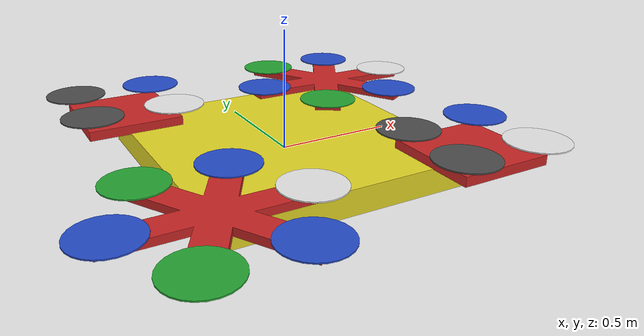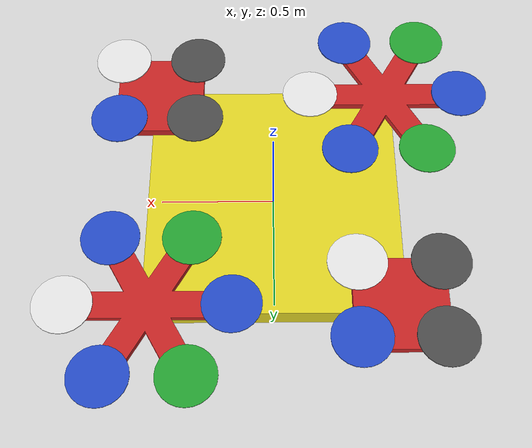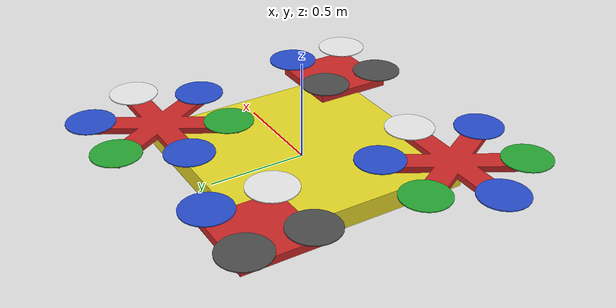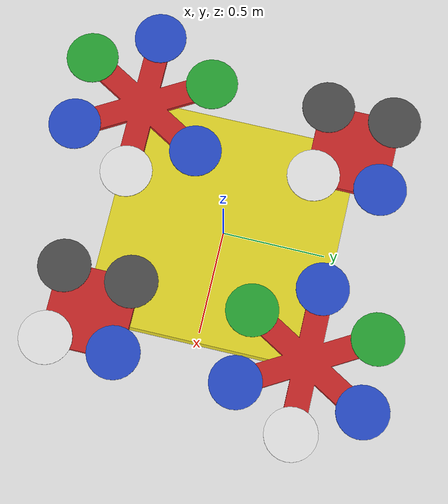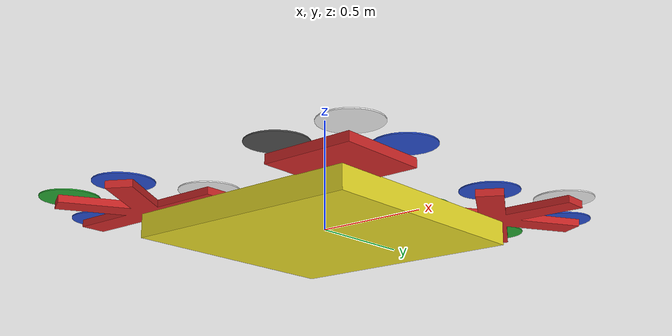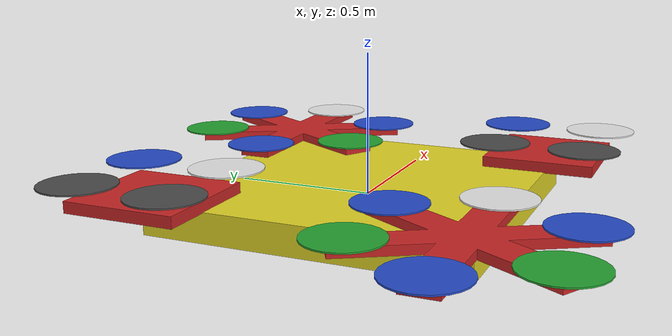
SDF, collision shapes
<sdf version='1.6'>
  <model name='quad_fl_parent'>
    <link name='base_link'>
      <pose frame=''>0 0 0 0 -0 0</pose>
      <inertial>
        <pose frame=''>0 0 0 0 -0 0</pose>
        <mass>0.75</mass>
        <inertia>
          <ixx>0.06906</ixx>
          <ixy>0</ixy>
          <ixz>0</ixz>
          <iyy>0.06906</iyy>
          <iyz>0</iyz>
          <izz>0.136899</izz>
        </inertia>
      </inertial>
      <collision name='base_link_inertia_collision'>
        <pose frame=''>0 0 0 0 -0 0</pose>
        <geometry>
          <box>
            <size>1.11 1.11 0.105</size>
          </box>
        </geometry>
        <surface>
          <contact>
            <ode>
              <min_depth>0.001</min_depth>
              <max_vel>0</max_vel>
            </ode>
          </contact>
          <friction>
            <ode/>
          </friction>
        </surface>
      </collision>
      <visual name='base_link_inertia_visual'>
        <pose frame=''>0 0 0 -1.570795 -0 1.570795</pose>
        <geometry>
          <mesh>
            <scale>0.003165 0.003165 0.003165</scale>
            <uri>model://quad_fl_parent/meshes/body_parent_new.stl</uri>
          </mesh>
        </geometry>
        <material>
          <script>
            <name>Gazebo/Yellow</name>
            <uri>file://media/materials/scripts/gazebo.material</uri>
          </script>
        </material>
      </visual>
      <gravity>1</gravity>
      <velocity_decay/>
    </link>

    <link name='/imu_link'>
      <pose frame=''>0 0 0 0 -0 0</pose>
      <inertial>
          <pose frame=''>0 0 0 0 -0 0</pose>
          <mass>0.015</mass>
          <inertia>
              <ixx>1e-05</ixx>
              <ixy>0</ixy>
              <ixz>0</ixz>
              <iyy>1e-05</iyy>
              <iyz>0</iyz>
              <izz>1e-05</izz>
          </inertia>
      </inertial>
    </link>
    <joint name='/imu_joint' type='revolute'>
      <child>/imu_link</child>
      <parent>base_link</parent>
      <axis>
          <xyz>1 0 0</xyz>
          <limit>
              <lower>0</lower>
              <upper>0</upper>
              <effort>0</effort>
              <velocity>0</velocity>
          </limit>
          <dynamics>
              <spring_reference>0</spring_reference>
              <spring_stiffness>0</spring_stiffness>
          </dynamics>
          <use_parent_model_frame>1</use_parent_model_frame>
      </axis>
    </joint>

    <static>0</static>

     <include>
      <uri>model://hex_fl_rr</uri>
      <pose frame=''>-0.525 -0.525 0.07 0 -0 0</pose>
    </include>
    <joint name="hex_fl_rr_link" type="fixed">
      <parent>base_link</parent>
      <child>hex_fl_rr::base_link</child>
    </joint>

    <include>
      <uri>model://quad_fl_rl</uri>
      <pose frame=''>-0.525 0.525 0.07 0 -0 0</pose>
    </include>
    <joint name="quad_fl_rl_link" type="fixed">
      <parent>base_link</parent>
      <child>quad_fl_rl::base_link</child>
    </joint>

    <include>
      <uri>model://quad_fl_fr</uri>
      <pose frame=''>0.525 -0.525 0.07 0 -0 0</pose>
    </include>
    <joint name="quad_fl_fr_link" type="fixed">
      <parent>base_link</parent>
      <child>quad_fl_fr::base_link</child>
    </joint>

    <include>
      <uri>model://hex_fl_fl</uri>
      <pose frame=''>0.525 0.525 0.07 0 -0 0</pose>
    </include>
    <joint name="hex_fl_fl_link" type="fixed">
      <parent>base_link</parent>
      <child>hex_fl_fl::base_link</child>
    </joint>

    <plugin name='gps_plugin' filename='libgazebo_gps_plugin.so'>
      <robotNamespace>quad_fl_parent</robotNamespace>
      <gpsNoise>1</gpsNoise>
    </plugin>
    <plugin name='magnetometer_plugin' filename='libgazebo_magnetometer_plugin.so'>
      <robotNamespace>quad_fl_parent</robotNamespace>
      <pubRate>20</pubRate>
      <noiseDensity>0.0004</noiseDensity>
      <randomWalk>6.4e-06</randomWalk>
      <biasCorrelationTime>600</biasCorrelationTime>
      <magTopic>/mag</magTopic>
    </plugin>
    <plugin name='barometer_plugin' filename='libgazebo_barometer_plugin.so'>
      <robotNamespace>quad_fl_parent</robotNamespace>
      <pubRate>10</pubRate>
      <baroTopic>/baro</baroTopic>
    </plugin>
    <plugin name='mavlink_interface' filename='libgazebo_mavlink_interface.so'>
      <robotNamespace>quad_fl_parent</robotNamespace>
      <imuSubTopic>/imu</imuSubTopic>
      <gpsSubTopic>/gps</gpsSubTopic>
      <magSubTopic>/mag</magSubTopic>
      <baroSubTopic>/baro</baroSubTopic>
      <mavlink_addr>INADDR_ANY</mavlink_addr>
      <mavlink_udp_port>14071</mavlink_udp_port>
      <mavlink_tcp_port>4571</mavlink_tcp_port>
      <serialEnabled>0</serialEnabled>
      <serialDevice>/dev/ttyACM0</serialDevice>
      <baudRate>921600</baudRate>
      <qgc_addr>INADDR_ANY</qgc_addr>
      <qgc_udp_port>14561</qgc_udp_port>
      <sdk_addr>INADDR_ANY</sdk_addr>
      <sdk_udp_port>13661</sdk_udp_port>
      <hil_mode>0</hil_mode>
      <hil_state_level>0</hil_state_level>
      <vehicle_is_tailsitter>0</vehicle_is_tailsitter>
      <send_vision_estimation>1</send_vision_estimation>
      <send_odometry>0</send_odometry>
      <enable_lockstep>1</enable_lockstep>
      <use_tcp>1</use_tcp>
      <motorSpeedCommandPubTopic>/gazebo/command/motor_speed</motorSpeedCommandPubTopic>
      <control_channels>
        <channel name='rotor1'>
          <input_index>0</input_index>
          <input_offset>0</input_offset>
          <input_scaling>1000</input_scaling>
          <zero_position_disarmed>0</zero_position_disarmed>
          <zero_position_armed>100</zero_position_armed>
          <joint_control_type>velocity</joint_control_type>
        </channel>
        <channel name='rotor2'>
          <input_index>1</input_index>
          <input_offset>0</input_offset>
          <input_scaling>1000</input_scaling>
          <zero_position_disarmed>0</zero_position_disarmed>
          <zero_position_armed>100</zero_position_armed>
          <joint_control_type>velocity</joint_control_type>
        </channel>
        <channel name='rotor3'>
          <input_index>2</input_index>
          <input_offset>0</input_offset>
          <input_scaling>1000</input_scaling>
          <zero_position_disarmed>0</zero_position_disarmed>
          <zero_position_armed>100</zero_position_armed>
          <joint_control_type>velocity</joint_control_type>
        </channel>
        <channel name='rotor4'>
          <input_index>3</input_index>
          <input_offset>0</input_offset>
          <input_scaling>1000</input_scaling>
          <zero_position_disarmed>0</zero_position_disarmed>
          <zero_position_armed>100</zero_position_armed>
          <joint_control_type>velocity</joint_control_type>
        </channel>
      </control_channels>
    </plugin>
    <static>0</static>
    <plugin name='rotors_gazebo_imu_plugin' filename='libgazebo_imu_plugin.so'>
      <robotNamespace>quad_fl_parent</robotNamespace>
      <linkName>/imu_link</linkName>
      <imuTopic>/imu</imuTopic>
      <gyroscopeNoiseDensity>0.0003394</gyroscopeNoiseDensity>
      <gyroscopeRandomWalk>3.8785e-05</gyroscopeRandomWalk>
      <gyroscopeBiasCorrelationTime>1000.0</gyroscopeBiasCorrelationTime>
      <gyroscopeTurnOnBiasSigma>0.0087</gyroscopeTurnOnBiasSigma>
      <accelerometerNoiseDensity>0.004</accelerometerNoiseDensity>
      <accelerometerRandomWalk>0.006</accelerometerRandomWalk>
      <accelerometerBiasCorrelationTime>300.0</accelerometerBiasCorrelationTime>
      <accelerometerTurnOnBiasSigma>0.196</accelerometerTurnOnBiasSigma>
    </plugin>

  </model>

</sdf>

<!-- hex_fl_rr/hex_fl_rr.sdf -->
<sdf version='1.6'>
  <model name='hex_fl_rr'>
    <link name='base_link'>
      <pose frame=''>0 0 0 0 -0 0</pose>
      <inertial>
        <pose frame=''>0 0 0 0 -0 0</pose>
        <mass>2.0</mass>
        <inertia>
          <ixx>0.0818</ixx>
          <ixy>0</ixy>
          <ixz>0</ixz>
          <iyy>0.0818</iyy>
          <iyz>0</iyz>
          <izz>0.1633</izz>
        </inertia>
      </inertial>
      <collision name='base_link_inertia_collision'>
        <pose frame=''>0 0 0.015 -1.570795 -0 1.570795</pose>
        <geometry>
          <mesh>
            <scale>0.001055 0.001055 0.001055</scale>
            <uri>model://hex_fl_rr/meshes/hex_collision.stl</uri>
          </mesh>
        </geometry>
        <surface>
          <contact>
            <ode>
              <min_depth>0.001</min_depth>
              <max_vel>0</max_vel>
            </ode>
          </contact>
          <friction>
            <ode/>
          </friction>
        </surface>
      </collision>
      <visual name='base_link_inertia_visual'>
        <pose frame=''>0 0 0 -1.570795 -0 1.570795</pose>
        <geometry>
          <mesh>
            <scale>0.001055 0.001055 0.001055</scale>
            <uri>model://hex_fl_rr/meshes/hex_frame.stl</uri>
          </mesh>
        </geometry>
        <material>
          <script>
            <name>Gazebo/Red</name>
            <uri>file://media/materials/scripts/gazebo.material</uri>
          </script>
        </material>
      </visual>
      <gravity>1</gravity>
      <velocity_decay/>
    </link>
    <link name='/imu_link'>
      <pose frame=''>0 0 0 0 -0 0</pose>
      <inertial>
        <pose frame=''>0 0 0 0 -0 0</pose>
        <mass>0.015</mass>
        <inertia>
          <ixx>1e-05</ixx>
          <ixy>0</ixy>
          <ixz>0</ixz>
          <iyy>1e-05</iyy>
          <iyz>0</iyz>
          <izz>1e-05</izz>
        </inertia>
      </inertial>
    </link>
    <joint name='/imu_joint' type='revolute'>
      <child>/imu_link</child>
      <parent>base_link</parent>
      <axis>
        <xyz>1 0 0</xyz>
        <limit>
          <lower>0</lower>
          <upper>0</upper>
          <effort>0</effort>
          <velocity>0</velocity>
        </limit>
        <dynamics>
          <spring_reference>0</spring_reference>
          <spring_stiffness>0</spring_stiffness>
        </dynamics>
        <use_parent_model_frame>1</use_parent_model_frame>
      </axis>
    </joint>

    <link name='rotor_3'>
      <pose frame=''>0.175 -0.30311 0.022 0 -0 0</pose>
      <inertial>
        <pose frame=''>0 0 0 0 -0 0</pose>
        <mass>0.005</mass>
        <inertia>
          <ixx>9.75e-07</ixx>
          <ixy>0</ixy>
          <ixz>0</ixz>
          <iyy>0.000273104</iyy>
          <iyz>0</iyz>
          <izz>0.000274004</izz>
        </inertia>
      </inertial>
      <collision name='rotor_3_collision'>
        <pose frame=''>0 0 0 0 -0 0</pose>
        <geometry>
          <cylinder>
            <length>0.005</length>
            <radius>0.128</radius>
          </cylinder>
        </geometry>
        <surface>
          <contact>
            <ode/>
          </contact>
          <friction>
            <ode/>
          </friction>
        </surface>
      </collision>
      <visual name='rotor_3_visual'>
        <pose frame=''>0 0 0 0 -0 0</pose>
        <geometry>
          <mesh>
            <scale>1 1 1</scale>
            <uri>model://rotors_description/meshes/iris_prop_ccw.dae</uri>
          </mesh>
        </geometry>
        <material>
          <script>
            <name>Gazebo/Blue</name>
            <uri>file://media/materials/scripts/gazebo.material</uri>
          </script>
        </material>
      </visual>
      <gravity>1</gravity>
      <velocity_decay/>
    </link>
    <joint name='rotor_3_joint' type='revolute'>
      <child>rotor_3</child>
      <parent>base_link</parent>
      <axis>
        <xyz>0 0 1</xyz>
        <limit>
          <lower>-1e+16</lower>
          <upper>1e+16</upper>
        </limit>
        <dynamics>
          <spring_reference>0</spring_reference>
          <spring_stiffness>0</spring_stiffness>
        </dynamics>
        <use_parent_model_frame>1</use_parent_model_frame>
      </axis>
    </joint>
    <link name='rotor_4'>
      <pose frame=''>0.175 0.30311 0.022 0 -0 0</pose>
      <inertial>
        <pose frame=''>0 0 0 0 -0 0</pose>
        <mass>0.005</mass>
        <inertia>
          <ixx>9.75e-07</ixx>
          <ixy>0</ixy>
          <ixz>0</ixz>
          <iyy>0.000273104</iyy>
          <iyz>0</iyz>
          <izz>0.000274004</izz>
        </inertia>
      </inertial>
      <collision name='rotor_4_collision'>
        <pose frame=''>0 0 0 0 -0 0</pose>
        <geometry>
          <cylinder>
            <length>0.005</length>
            <radius>0.128</radius>
          </cylinder>
        </geometry>
        <surface>
          <contact>
            <ode/>
          </contact>
          <friction>
            <ode/>
          </friction>
        </surface>
      </collision>
      <visual name='rotor_4_visual'>
        <pose frame=''>0 0 0 0 -0 0</pose>
        <geometry>
          <mesh>
            <scale>1 1 1</scale>
            <uri>model://rotors_description/meshes/iris_prop_ccw.dae</uri>
          </mesh>
        </geometry>
        <material>
          <script>
            <name>Gazebo/Blue</name>
            <uri>file://media/materials/scripts/gazebo.material</uri>
          </script>
        </material>
      </visual>
      <gravity>1</gravity>
      <velocity_decay/>
    </link>
    <joint name='rotor_4_joint' type='revolute'>
      <child>rotor_4</child>
      <parent>base_link</parent>
      <axis>
        <xyz>0 0 1</xyz>
        <limit>
          <lower>-1e+16</lower>
          <upper>1e+16</upper>
        </limit>
        <dynamics>
          <spring_reference>0</spring_reference>
          <spring_stiffness>0</spring_stiffness>
        </dynamics>
        <use_parent_model_frame>1</use_parent_model_frame>
      </axis>
    </joint>
    <link name='rotor_1'>
      <pose frame=''>-0.35 0 0.022 0 -0 0</pose>
      <inertial>
        <pose frame=''>0 0 0 0 -0 0</pose>
        <mass>0.005</mass>
        <inertia>
          <ixx>9.75e-07</ixx>
          <ixy>0</ixy>
          <ixz>0</ixz>
          <iyy>0.000273104</iyy>
          <iyz>0</iyz>
          <izz>0.000274004</izz>
        </inertia>
      </inertial>
      <collision name='rotor_1_collision'>
        <pose frame=''>0 0 0 0 -0 0</pose>
        <geometry>
          <cylinder>
            <length>0.005</length>
            <radius>0.128</radius>
          </cylinder>
        </geometry>
        <surface>
          <contact>
            <ode/>
          </contact>
          <friction>
            <ode/>
          </friction>
        </surface>
      </collision>
      <visual name='rotor_1_visual'>
        <pose frame=''>0 0 0 0 -0 0</pose>
        <geometry>
          <mesh>
            <scale>1 1 1</scale>
            <uri>model://rotors_description/meshes/iris_prop_ccw.dae</uri>
          </mesh>
        </geometry>
        <material>
          <script>
            <name>Gazebo/Blue</name>
            <uri>file://media/materials/scripts/gazebo.material</uri>
          </script>
        </material>
      </visual>
      <gravity>1</gravity>
      <velocity_decay/>
    </link>
    <joint name='rotor_1_joint' type='revolute'>
      <child>rotor_1</child>
      <parent>base_link</parent>
      <axis>
        <xyz>0 0 1</xyz>
        <limit>
          <lower>-1e+16</lower>
          <upper>1e+16</upper>
        </limit>
        <dynamics>
          <spring_reference>0</spring_reference>
          <spring_stiffness>0</spring_stiffness>
        </dynamics>
        <use_parent_model_frame>1</use_parent_model_frame>
      </axis>
    </joint>
    <link name='rotor_5'>
      <pose frame=''>-0.175 -0.30311 0.022 0 -0 0</pose>
      <inertial>
        <pose frame=''>0 0 0 0 -0 0</pose>
        <mass>0.005</mass>
        <inertia>
          <ixx>9.75e-07</ixx>
          <ixy>0</ixy>
          <ixz>0</ixz>
          <iyy>0.000273104</iyy>
          <iyz>0</iyz>
          <izz>0.000274004</izz>
        </inertia>
      </inertial>
      <collision name='rotor_5_collision'>
        <pose frame=''>0 0 0 0 -0 0</pose>
        <geometry>
          <cylinder>
            <length>0.005</length>
            <radius>0.128</radius>
          </cylinder>
        </geometry>
        <surface>
          <contact>
            <ode/>
          </contact>
          <friction>
            <ode/>
          </friction>
        </surface>
      </collision>
      <visual name='rotor_5_visual'>
        <pose frame=''>0 0 0 0 -0 0</pose>
        <geometry>
          <mesh>
            <scale>1 1 1</scale>
            <uri>model://rotors_description/meshes/iris_prop_cw.dae</uri>
          </mesh>
        </geometry>
        <material>
          <script>
            <name>Gazebo/Green</name>
            <uri>file://media/materials/scripts/gazebo.material</uri>
          </script>
        </material>
      </visual>
      <gravity>1</gravity>
      <velocity_decay/>
    </link>
    <joint name='rotor_5_joint' type='revolute'>
      <child>rotor_5</child>
      <parent>base_link</parent>
      <axis>
        <xyz>0 0 1</xyz>
        <limit>
          <lower>-1e+16</lower>
          <upper>1e+16</upper>
        </limit>
        <dynamics>
          <spring_reference>0</spring_reference>
          <spring_stiffness>0</spring_stiffness>
        </dynamics>
        <use_parent_model_frame>1</use_parent_model_frame>
      </axis>
    </joint>
    <link name='rotor_2'>
      <pose frame=''>-0.175 0.30311 0.022 0 -0 0</pose>
      <inertial>
        <pose frame=''>0 0 0 0 -0 0</pose>
        <mass>0.005</mass>
        <inertia>
          <ixx>9.75e-07</ixx>
          <ixy>0</ixy>
          <ixz>0</ixz>
          <iyy>0.000273104</iyy>
          <iyz>0</iyz>
          <izz>0.000274004</izz>
        </inertia>
      </inertial>
      <collision name='rotor_2_collision'>
        <pose frame=''>0 0 0 0 -0 0</pose>
        <geometry>
          <cylinder>
            <length>0.005</length>
            <radius>0.128</radius>
          </cylinder>
        </geometry>
        <surface>
          <contact>
            <ode/>
          </contact>
          <friction>
            <ode/>
          </friction>
        </surface>
      </collision>
      <visual name='rotor_2_visual'>
        <pose frame=''>0 0 0 0 -0 0</pose>
        <geometry>
          <mesh>
            <scale>1 1 1</scale>
            <uri>model://rotors_description/meshes/iris_prop_cw.dae</uri>
          </mesh>
        </geometry>
        <material>
          <script>
            <name>Gazebo/Green</name>
            <uri>file://media/materials/scripts/gazebo.material</uri>
          </script>
        </material>
      </visual>
      <gravity>1</gravity>
      <velocity_decay/>
    </link>
    <joint name='rotor_2_joint' type='revolute'>
      <child>rotor_2</child>
      <parent>base_link</parent>
      <axis>
        <xyz>0 0 1</xyz>
        <limit>
          <lower>-1e+16</lower>
          <upper>1e+16</upper>
        </limit>
        <dynamics>
          <spring_reference>0</spring_reference>
          <spring_stiffness>0</spring_stiffness>
        </dynamics>
        <use_parent_model_frame>1</use_parent_model_frame>
      </axis>
    </joint>
    <link name='rotor_0'>
      <pose frame=''>0.35 0 0.022 0 -0 0</pose>
      <inertial>
        <pose frame=''>0 0 0 0 -0 0</pose>
        <mass>0.005</mass>
        <inertia>
          <ixx>9.75e-07</ixx>
          <ixy>0</ixy>
          <ixz>0</ixz>
          <iyy>0.000273104</iyy>
          <iyz>0</iyz>
          <izz>0.000274004</izz>
        </inertia>
      </inertial>
      <collision name='rotor_0_collision'>
        <pose frame=''>0 0 0 0 -0 0</pose>
        <geometry>
          <cylinder>
            <length>0.005</length>
            <radius>0.128</radius>
          </cylinder>
        </geometry>
        <surface>
          <contact>
            <ode/>
          </contact>
          <friction>
            <ode/>
          </friction>
        </surface>
      </collision>
      <visual name='rotor_0_visual'>
        <pose frame=''>0 0 0 0 -0 0</pose>
        <geometry>
          <mesh>
            <scale>1 1 1</scale>
            <uri>model://rotors_description/meshes/iris_prop_cw.dae</uri>
          </mesh>
        </geometry>
        <material>
          <script>
            <name>Gazebo/White</name>
            <uri>file://media/materials/scripts/gazebo.material</uri>
          </script>
        </material>
      </visual>
      <gravity>1</gravity>
      <velocity_decay/>
    </link>
    <joint name='rotor_0_joint' type='revolute'>
      <child>rotor_0</child>
      <parent>base_link</parent>
      <axis>
        <xyz>0 0 1</xyz>
        <limit>
          <lower>-1e+16</lower>
          <upper>1e+16</upper>
        </limit>
        <dynamics>
          <spring_reference>0</spring_reference>
          <spring_stiffness>0</spring_stiffness>
        </dynamics>
        <use_parent_model_frame>1</use_parent_model_frame>
      </axis>
    </joint>

    <plugin name='rosbag' filename='libgazebo_multirotor_base_plugin.so'>
      <robotNamespace>hex_fl_rr</robotNamespace>
      <linkName>base_link</linkName>
      <rotorVelocitySlowdownSim>10</rotorVelocitySlowdownSim>
    </plugin>
    <plugin name='front_motor_model' filename='libgazebo_motor_model.so'>
      <robotNamespace>hex_fl_rr</robotNamespace>
      <jointName>rotor_0_joint</jointName>
      <linkName>rotor_0</linkName>
      <turningDirection>cw</turningDirection>
      <timeConstantUp>0.0125</timeConstantUp>
      <timeConstantDown>0.025</timeConstantDown>
      <maxRotVelocity>1100</maxRotVelocity>
      <motorConstant>8.54858e-06</motorConstant>
      <momentConstant>0.06</momentConstant>
      <commandSubTopic>/gazebo/command/motor_speed</commandSubTopic>
      <motorNumber>0</motorNumber>
      <rotorDragCoefficient>0.000175</rotorDragCoefficient>
      <rollingMomentCoefficient>1e-06</rollingMomentCoefficient>
      <motorSpeedPubTopic>/motor_speed/0</motorSpeedPubTopic>
      <rotorVelocitySlowdownSim>10</rotorVelocitySlowdownSim>
    </plugin>
    <plugin name='back_motor_model' filename='libgazebo_motor_model.so'>
      <robotNamespace>hex_fl_rr</robotNamespace>
      <jointName>rotor_1_joint</jointName>
      <linkName>rotor_1</linkName>
      <turningDirection>ccw</turningDirection>
      <timeConstantUp>0.0125</timeConstantUp>
      <timeConstantDown>0.025</timeConstantDown>
      <maxRotVelocity>1100</maxRotVelocity>
      <motorConstant>8.54858e-06</motorConstant>
      <momentConstant>0.06</momentConstant>
      <commandSubTopic>/gazebo/command/motor_speed</commandSubTopic>
      <motorNumber>1</motorNumber>
      <rotorDragCoefficient>0.000175</rotorDragCoefficient>
      <rollingMomentCoefficient>1e-06</rollingMomentCoefficient>
      <motorSpeedPubTopic>/motor_speed/1</motorSpeedPubTopic>
      <rotorVelocitySlowdownSim>10</rotorVelocitySlowdownSim>
    </plugin>
    <plugin name='back_left_motor_model' filename='libgazebo_motor_model.so'>
      <robotNamespace>hex_fl_rr</robotNamespace>
      <jointName>rotor_2_joint</jointName>
      <linkName>rotor_2</linkName>
      <turningDirection>cw</turningDirection>
      <timeConstantUp>0.0125</timeConstantUp>
      <timeConstantDown>0.025</timeConstantDown>
      <maxRotVelocity>1100</maxRotVelocity>
      <motorConstant>8.54858e-06</motorConstant>
      <momentConstant>0.06</momentConstant>
      <commandSubTopic>/gazebo/command/motor_speed</commandSubTopic>
      <motorNumber>2</motorNumber>
      <rotorDragCoefficient>0.000175</rotorDragCoefficient>
      <rollingMomentCoefficient>1e-06</rollingMomentCoefficient>
      <motorSpeedPubTopic>/motor_speed/2</motorSpeedPubTopic>
      <rotorVelocitySlowdownSim>10</rotorVelocitySlowdownSim>
    </plugin>
    <plugin name='top_right_motor_model' filename='libgazebo_motor_model.so'>
      <robotNamespace>hex_fl_rr</robotNamespace>
      <jointName>rotor_3_joint</jointName>
      <linkName>rotor_3</linkName>
      <turningDirection>ccw</turningDirection>
      <timeConstantUp>0.0125</timeConstantUp>
      <timeConstantDown>0.025</timeConstantDown>
      <maxRotVelocity>1100</maxRotVelocity>
      <motorConstant>8.54858e-06</motorConstant>
      <momentConstant>0.06</momentConstant>
      <commandSubTopic>/gazebo/command/motor_speed</commandSubTopic>
      <motorNumber>3</motorNumber>
      <rotorDragCoefficient>0.000175</rotorDragCoefficient>
      <rollingMomentCoefficient>1e-06</rollingMomentCoefficient>
      <motorSpeedPubTopic>/motor_speed/3</motorSpeedPubTopic>
      <rotorVelocitySlowdownSim>10</rotorVelocitySlowdownSim>
    </plugin>
    <plugin name='top_left_motor_model' filename='libgazebo_motor_model.so'>
      <robotNamespace>hex_fl_rr</robotNamespace>
      <jointName>rotor_4_joint</jointName>
      <linkName>rotor_4</linkName>
      <turningDirection>ccw</turningDirection>
      <timeConstantUp>0.0125</timeConstantUp>
      <timeConstantDown>0.025</timeConstantDown>
      <maxRotVelocity>1100</maxRotVelocity>
      <motorConstant>8.54858e-06</motorConstant>
      <momentConstant>0.06</momentConstant>
      <commandSubTopic>/gazebo/command/motor_speed</commandSubTopic>
      <motorNumber>4</motorNumber>
      <rotorDragCoefficient>0.000175</rotorDragCoefficient>
      <rollingMomentCoefficient>1e-06</rollingMomentCoefficient>
      <motorSpeedPubTopic>/motor_speed/4</motorSpeedPubTopic>
      <rotorVelocitySlowdownSim>10</rotorVelocitySlowdownSim>
    </plugin>
    <plugin name='back_right_motor_model' filename='libgazebo_motor_model.so'>
      <robotNamespace>hex_fl_rr</robotNamespace>
      <jointName>rotor_5_joint</jointName>
      <linkName>rotor_5</linkName>
      <turningDirection>cw</turningDirection>
      <timeConstantUp>0.0125</timeConstantUp>
      <timeConstantDown>0.025</timeConstantDown>
      <maxRotVelocity>1100</maxRotVelocity>
      <motorConstant>8.54858e-06</motorConstant>
      <momentConstant>0.06</momentConstant>
      <commandSubTopic>/gazebo/command/motor_speed</commandSubTopic>
      <motorNumber>5</motorNumber>
      <rotorDragCoefficient>0.000175</rotorDragCoefficient>
      <rollingMomentCoefficient>1e-06</rollingMomentCoefficient>
      <motorSpeedPubTopic>/motor_speed/5</motorSpeedPubTopic>
      <rotorVelocitySlowdownSim>10</rotorVelocitySlowdownSim>
    </plugin>

    <plugin name='gps_plugin' filename='libgazebo_gps_plugin.so'>
      <robotNamespace>hex_fl_rr</robotNamespace>
      <gpsNoise>1</gpsNoise>
    </plugin>
    <plugin name='magnetometer_plugin' filename='libgazebo_magnetometer_plugin.so'>
      <robotNamespace>hex_fl_rr</robotNamespace>
      <pubRate>20</pubRate>
      <noiseDensity>0.0004</noiseDensity>
      <randomWalk>6.4e-06</randomWalk>
      <biasCorrelationTime>600</biasCorrelationTime>
      <magTopic>/mag</magTopic>
    </plugin>
    <plugin name='barometer_plugin' filename='libgazebo_barometer_plugin.so'>
      <robotNamespace>hex_fl_rr</robotNamespace>
      <pubRate>10</pubRate>
      <baroTopic>/baro</baroTopic>
    </plugin>
    <plugin name='mavlink_interface' filename='libgazebo_mavlink_interface.so'>
      <robotNamespace>hex_fl_rr</robotNamespace>
      <imuSubTopic>/imu</imuSubTopic>
      <gpsSubTopic>/gps</gpsSubTopic>
      <magSubTopic>/mag</magSubTopic>
      <baroSubTopic>/baro</baroSubTopic>
      <mavlink_addr>INADDR_ANY</mavlink_addr>
      <mavlink_udp_port>14075</mavlink_udp_port>
      <mavlink_tcp_port>4575</mavlink_tcp_port>
      <serialEnabled>0</serialEnabled>
      <serialDevice>/dev/ttyACM0</serialDevice>
      <baudRate>921600</baudRate>
      <qgc_addr>INADDR_ANY</qgc_addr>
      <qgc_udp_port>14565</qgc_udp_port>
      <sdk_addr>INADDR_ANY</sdk_addr>
      <sdk_udp_port>13665</sdk_udp_port>
      <hil_mode>0</hil_mode>
      <hil_state_level>0</hil_state_level>
      <vehicle_is_tailsitter>0</vehicle_is_tailsitter>
      <send_vision_estimation>1</send_vision_estimation>
      <send_odometry>0</send_odometry>
      <enable_lockstep>1</enable_lockstep>
      <use_tcp>1</use_tcp>
      <motorSpeedCommandPubTopic>/gazebo/command/motor_speed</motorSpeedCommandPubTopic>
      <control_channels>
        <channel name='rotor0'>
          <input_index>0</input_index>
          <input_offset>0</input_offset>
          <input_scaling>1000</input_scaling>
          <zero_position_disarmed>0</zero_position_disarmed>
          <zero_position_armed>100</zero_position_armed>
          <joint_control_type>velocity</joint_control_type>
        </channel>
        <channel name='rotor1'>
          <input_index>1</input_index>
          <input_offset>0</input_offset>
          <input_scaling>1000</input_scaling>
          <zero_position_disarmed>0</zero_position_disarmed>
          <zero_position_armed>100</zero_position_armed>
          <joint_control_type>velocity</joint_control_type>
        </channel>
        <channel name='rotor2'>
          <input_index>2</input_index>
          <input_offset>0</input_offset>
          <input_scaling>1000</input_scaling>
          <zero_position_disarmed>0</zero_position_disarmed>
          <zero_position_armed>100</zero_position_armed>
          <joint_control_type>velocity</joint_control_type>
        </channel>
        <channel name='rotor3'>
          <input_index>3</input_index>
          <input_offset>0</input_offset>
          <input_scaling>1000</input_scaling>
          <zero_position_disarmed>0</zero_position_disarmed>
          <zero_position_armed>100</zero_position_armed>
          <joint_control_type>velocity</joint_control_type>
        </channel>
        <channel name='rotor4'>
          <input_index>4</input_index>
          <input_offset>0</input_offset>
          <input_scaling>1000</input_scaling>
          <zero_position_disarmed>0</zero_position_disarmed>
          <zero_position_armed>100</zero_position_armed>
          <joint_control_type>velocity</joint_control_type>
        </channel>
        <channel name='rotor5'>
          <input_index>5</input_index>
          <input_offset>0</input_offset>
          <input_scaling>1000</input_scaling>
          <zero_position_disarmed>0</zero_position_disarmed>
          <zero_position_armed>100</zero_position_armed>
          <joint_control_type>velocity</joint_control_type>
        </channel>
      </control_channels>
    </plugin>
    <static>0</static>
    <plugin name='rotors_gazebo_imu_plugin' filename='libgazebo_imu_plugin.so'>
      <robotNamespace>hex_fl_rr</robotNamespace>
      <linkName>/imu_link</linkName>
      <imuTopic>/imu</imuTopic>
      <gyroscopeNoiseDensity>0.0003394</gyroscopeNoiseDensity>
      <gyroscopeRandomWalk>3.8785e-05</gyroscopeRandomWalk>
      <gyroscopeBiasCorrelationTime>1000.0</gyroscopeBiasCorrelationTime>
      <gyroscopeTurnOnBiasSigma>0.0087</gyroscopeTurnOnBiasSigma>
      <accelerometerNoiseDensity>0.004</accelerometerNoiseDensity>
      <accelerometerRandomWalk>0.006</accelerometerRandomWalk>
      <accelerometerBiasCorrelationTime>300.0</accelerometerBiasCorrelationTime>
      <accelerometerTurnOnBiasSigma>0.196</accelerometerTurnOnBiasSigma>
    </plugin>

  </model>
</sdf>

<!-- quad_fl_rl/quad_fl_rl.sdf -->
<sdf version='1.6'>
  <model name='quad_fl_rl'>
    <link name='base_link'>
      <pose frame=''>0 0 0 0 -0 0</pose>
      <inertial>
        <pose frame=''>0 0 0 0 -0 0</pose>
        <mass>1.0</mass>
        <inertia>
          <ixx>0.0134667</ixx>
          <ixy>0</ixy>
          <ixz>0</ixz>
          <iyy>0.0134667</iyy>
          <iyz>0</iyz>
          <izz>0.02667</izz>
        </inertia>
      </inertial>
      <collision name='base_link_inertia_collision'>
        <pose frame=''>0 0 0.00 0 -0 0</pose>
        <geometry>
          <box>
            <size>0.4 0.4 0.04</size>
          </box>
        </geometry>
        <surface>
          <contact>
            <ode>
              <min_depth>0.001</min_depth>
              <max_vel>0</max_vel>
            </ode>
          </contact>
          <friction>
            <ode/>
          </friction>
        </surface>
      </collision>
      <visual name='base_link_inertia_visual'>
        <pose frame=''>0 0 0 -1.570795 -0 1.570795</pose>
        <geometry>
          <mesh>
            <scale>0.001055 0.001055 0.001055</scale>
            <uri>model://quad_fl_rl/meshes/body.stl</uri>
          </mesh>
        </geometry>
        <material>
          <script>
            <name>Gazebo/Red</name>
            <uri>file://media/materials/scripts/gazebo.material</uri>
          </script>
        </material>
      </visual>
      <gravity>1</gravity>
      <velocity_decay/>
    </link>
    <link name='/imu_link'>
      <pose frame=''>0 0 0 0 -0 0</pose>
      <inertial>
        <pose frame=''>0 0 0 0 -0 0</pose>
        <mass>0.015</mass>
        <inertia>
          <ixx>1e-05</ixx>
          <ixy>0</ixy>
          <ixz>0</ixz>
          <iyy>1e-05</iyy>
          <iyz>0</iyz>
          <izz>1e-05</izz>
        </inertia>
      </inertial>
    </link>
    <joint name='/imu_joint' type='revolute'>
      <child>/imu_link</child>
      <parent>base_link</parent>
      <axis>
        <xyz>1 0 0</xyz>
        <limit>
          <lower>0</lower>
          <upper>0</upper>
          <effort>0</effort>
          <velocity>0</velocity>
        </limit>
        <dynamics>
          <spring_reference>0</spring_reference>
          <spring_stiffness>0</spring_stiffness>
        </dynamics>
        <use_parent_model_frame>1</use_parent_model_frame>
      </axis>
    </joint>
    <link name='rotor_0'>
      <pose frame=''>0.178 -0.163 0.07 0 -0 0</pose>
      <inertial>
        <pose frame=''>0 0 0 0 -0 0</pose>
        <mass>0.005</mass>
        <inertia>
          <ixx>9.75e-07</ixx>
          <ixy>0</ixy>
          <ixz>0</ixz>
          <iyy>0.000273104</iyy>
          <iyz>0</iyz>
          <izz>0.000274004</izz>
        </inertia>
      </inertial>
      <collision name='rotor_0_collision'>
        <pose frame=''>0 0 0 0 -0 0</pose>
        <geometry>
          <cylinder>
            <length>0.005</length>
            <radius>0.128</radius>
          </cylinder>
        </geometry>
        <surface>
          <contact>
            <ode/>
          </contact>
          <friction>
            <ode/>
          </friction>
        </surface>
      </collision>
      <visual name='rotor_0_visual'>
        <pose frame=''>0 0 0 0 -0 0</pose>
        <geometry>
          <mesh>
            <scale>1 1 1</scale>
            <uri>model://rotors_description/meshes/iris_prop_cw.dae</uri>
          </mesh>
        </geometry>
        <material>
          <script>
            <name>Gazebo/White</name>
            <uri>file://media/materials/scripts/gazebo.material</uri>
          </script>
        </material>
      </visual>
      <gravity>1</gravity>
      <velocity_decay/>
    </link>
    <joint name='rotor_0_joint' type='revolute'>
      <child>rotor_0</child>
      <parent>base_link</parent>
      <axis>
        <xyz>0 0 1</xyz>
        <limit>
          <lower>-1e+16</lower>
          <upper>1e+16</upper>
        </limit>
        <dynamics>
          <spring_reference>0</spring_reference>
          <spring_stiffness>0</spring_stiffness>
        </dynamics>
        <use_parent_model_frame>1</use_parent_model_frame>
      </axis>
    </joint>
    <link name='rotor_1'>
      <pose frame=''>-0.17 0.1635 0.07 0 -0 0</pose>
      <inertial>
        <pose frame=''>0 0 0 0 -0 0</pose>
        <mass>0.005</mass>
        <inertia>
          <ixx>9.75e-07</ixx>
          <ixy>0</ixy>
          <ixz>0</ixz>
          <iyy>0.000273104</iyy>
          <iyz>0</iyz>
          <izz>0.000274004</izz>
        </inertia>
      </inertial>
      <collision name='rotor_1_collision'>
        <pose frame=''>0 0 0 0 -0 0</pose>
        <geometry>
          <cylinder>
            <length>0.005</length>
            <radius>0.128</radius>
          </cylinder>
        </geometry>
        <surface>
          <contact>
            <ode/>
          </contact>
          <friction>
            <ode/>
          </friction>
        </surface>
      </collision>
      <visual name='rotor_1_visual'>
        <pose frame=''>0 0 0 0 -0 0</pose>
        <geometry>
          <mesh>
            <scale>1 1 1</scale>
            <uri>model://rotors_description/meshes/iris_prop_ccw.dae</uri>
          </mesh>
        </geometry>
        <material>
          <script>
            <name>Gazebo/DarkGrey</name>
            <uri>file://media/materials/scripts/gazebo.material</uri>
          </script>
        </material>
      </visual>
      <gravity>1</gravity>
      <velocity_decay/>
    </link>
    <joint name='rotor_1_joint' type='revolute'>
      <child>rotor_1</child>
      <parent>base_link</parent>
      <axis>
        <xyz>0 0 1</xyz>
        <limit>
          <lower>-1e+16</lower>
          <upper>1e+16</upper>
        </limit>
        <dynamics>
          <spring_reference>0</spring_reference>
          <spring_stiffness>0</spring_stiffness>
        </dynamics>
        <use_parent_model_frame>1</use_parent_model_frame>
      </axis>
    </joint>
    <link name='rotor_2'>
      <pose frame=''>0.175 0.163 0.07 0 -0 0</pose>
      <inertial>
        <pose frame=''>0 0 0 0 -0 0</pose>
        <mass>0.005</mass>
        <inertia>
          <ixx>9.75e-07</ixx>
          <ixy>0</ixy>
          <ixz>0</ixz>
          <iyy>0.000273104</iyy>
          <iyz>0</iyz>
          <izz>0.000274004</izz>
        </inertia>
      </inertial>
      <collision name='rotor_2_collision'>
        <pose frame=''>0 0 0 0 -0 0</pose>
        <geometry>
          <cylinder>
            <length>0.005</length>
            <radius>0.128</radius>
          </cylinder>
        </geometry>
        <surface>
          <contact>
            <ode/>
          </contact>
          <friction>
            <ode/>
          </friction>
        </surface>
      </collision>
      <visual name='rotor_2_visual'>
        <pose frame=''>0 0 0 0 -0 0</pose>
        <geometry>
          <mesh>
            <scale>1 1 1</scale>
            <uri>model://rotors_description/meshes/iris_prop_cw.dae</uri>
          </mesh>
        </geometry>
        <material>
          <script>
            <name>Gazebo/Blue</name>
            <uri>file://media/materials/scripts/gazebo.material</uri>
          </script>
        </material>
      </visual>
      <gravity>1</gravity>
      <velocity_decay/>
    </link>
    <joint name='rotor_2_joint' type='revolute'>
      <child>rotor_2</child>
      <parent>base_link</parent>
      <axis>
        <xyz>0 0 1</xyz>
        <limit>
          <lower>-1e+16</lower>
          <upper>1e+16</upper>
        </limit>
        <dynamics>
          <spring_reference>0</spring_reference>
          <spring_stiffness>0</spring_stiffness>
        </dynamics>
        <use_parent_model_frame>1</use_parent_model_frame>
      </axis>
    </joint>
    <link name='rotor_3'>
      <pose frame=''>-0.173 -0.1635 0.07 0 -0 0</pose>
      <inertial>
        <pose frame=''>0 0 0 0 -0 0</pose>
        <mass>0.005</mass>
        <inertia>
          <ixx>9.75e-07</ixx>
          <ixy>0</ixy>
          <ixz>0</ixz>
          <iyy>0.000273104</iyy>
          <iyz>0</iyz>
          <izz>0.000274004</izz>
        </inertia>
      </inertial>
      <collision name='rotor_3_collision'>
        <pose frame=''>0 0 0 0 -0 0</pose>
        <geometry>
          <cylinder>
            <length>0.005</length>
            <radius>0.128</radius>
          </cylinder>
        </geometry>
        <surface>
          <contact>
            <ode/>
          </contact>
          <friction>
            <ode/>
          </friction>
        </surface>
      </collision>
      <visual name='rotor_3_visual'>
        <pose frame=''>0 0 0 0 -0 0</pose>
        <geometry>
          <mesh>
            <scale>1 1 1</scale>
            <uri>model://rotors_description/meshes/iris_prop_ccw.dae</uri>
          </mesh>
        </geometry>
        <material>
          <script>
            <name>Gazebo/DarkGrey</name>
            <uri>file://media/materials/scripts/gazebo.material</uri>
          </script>
        </material>
      </visual>
      <gravity>1</gravity>
      <velocity_decay/>
    </link>
    <joint name='rotor_3_joint' type='revolute'>
      <child>rotor_3</child>
      <parent>base_link</parent>
      <axis>
        <xyz>0 0 1</xyz>
        <limit>
          <lower>-1e+16</lower>
          <upper>1e+16</upper>
        </limit>
        <dynamics>
          <spring_reference>0</spring_reference>
          <spring_stiffness>0</spring_stiffness>
        </dynamics>
        <use_parent_model_frame>1</use_parent_model_frame>
      </axis>
    </joint>

  <plugin name='rosbag' filename='libgazebo_multirotor_base_plugin.so'>
    <robotNamespace>quad_fl_rl</robotNamespace>
    <linkName>base_link</linkName>
      <rotorVelocitySlowdownSim>10</rotorVelocitySlowdownSim>
    </plugin>
    <plugin name='front_right_motor_model' filename='libgazebo_motor_model.so'>
      <robotNamespace>quad_fl_rl</robotNamespace>
      <jointName>rotor_0_joint</jointName>
      <linkName>rotor_0</linkName>
      <turningDirection>cw</turningDirection>
      <timeConstantUp>0.0125</timeConstantUp>
      <timeConstantDown>0.025</timeConstantDown>
      <maxRotVelocity>1100</maxRotVelocity>
      <motorConstant>8.54858e-06</motorConstant>
      <momentConstant>0.06</momentConstant>
      <commandSubTopic>/gazebo/command/motor_speed</commandSubTopic>
      <motorNumber>0</motorNumber>
      <rotorDragCoefficient>0.000175</rotorDragCoefficient>
      <rollingMomentCoefficient>1e-06</rollingMomentCoefficient>
      <motorSpeedPubTopic>/motor_speed/0</motorSpeedPubTopic>
      <rotorVelocitySlowdownSim>10</rotorVelocitySlowdownSim>
    </plugin>
    <plugin name='back_left_motor_model' filename='libgazebo_motor_model.so'>
      <robotNamespace>quad_fl_rl</robotNamespace>
      <jointName>rotor_1_joint</jointName>
      <linkName>rotor_1</linkName>
      <turningDirection>cw</turningDirection>
      <timeConstantUp>0.0125</timeConstantUp>
      <timeConstantDown>0.025</timeConstantDown>
      <maxRotVelocity>1100</maxRotVelocity>
      <motorConstant>8.54858e-06</motorConstant>
      <momentConstant>0.06</momentConstant>
      <commandSubTopic>/gazebo/command/motor_speed</commandSubTopic>
      <motorNumber>1</motorNumber>
      <rotorDragCoefficient>0.000175</rotorDragCoefficient>
      <rollingMomentCoefficient>1e-06</rollingMomentCoefficient>
      <motorSpeedPubTopic>/motor_speed/1</motorSpeedPubTopic>
      <rotorVelocitySlowdownSim>10</rotorVelocitySlowdownSim>
    </plugin>
    <plugin name='front_left_motor_model' filename='libgazebo_motor_model.so'>
      <robotNamespace>quad_fl_rl</robotNamespace>
      <jointName>rotor_2_joint</jointName>
      <linkName>rotor_2</linkName>
      <turningDirection>ccw</turningDirection>
      <timeConstantUp>0.0125</timeConstantUp>
      <timeConstantDown>0.025</timeConstantDown>
      <maxRotVelocity>1100</maxRotVelocity>
      <motorConstant>8.54858e-06</motorConstant>
      <momentConstant>0.06</momentConstant>
      <commandSubTopic>/gazebo/command/motor_speed</commandSubTopic>
      <motorNumber>2</motorNumber>
      <rotorDragCoefficient>0.000175</rotorDragCoefficient>
      <rollingMomentCoefficient>1e-06</rollingMomentCoefficient>
      <motorSpeedPubTopic>/motor_speed/2</motorSpeedPubTopic>
      <rotorVelocitySlowdownSim>10</rotorVelocitySlowdownSim>
    </plugin>
    <plugin name='back_right_motor_model' filename='libgazebo_motor_model.so'>
      <robotNamespace>quad_fl_rl</robotNamespace>
      <jointName>rotor_3_joint</jointName>
      <linkName>rotor_3</linkName>
      <turningDirection>ccw</turningDirection>
      <timeConstantUp>0.0125</timeConstantUp>
      <timeConstantDown>0.025</timeConstantDown>
      <maxRotVelocity>1100</maxRotVelocity>
      <motorConstant>8.54858e-06</motorConstant>
      <momentConstant>0.06</momentConstant>
      <commandSubTopic>/gazebo/command/motor_speed</commandSubTopic>
      <motorNumber>3</motorNumber>
      <rotorDragCoefficient>0.000175</rotorDragCoefficient>
      <rollingMomentCoefficient>1e-06</rollingMomentCoefficient>
      <motorSpeedPubTopic>/motor_speed/3</motorSpeedPubTopic>
      <rotorVelocitySlowdownSim>10</rotorVelocitySlowdownSim>
    </plugin>

    <plugin name='gps_plugin' filename='libgazebo_gps_plugin.so'>
      <robotNamespace>quad_fl_rl</robotNamespace>
      <gpsNoise>1</gpsNoise>
    </plugin>
    <plugin name='magnetometer_plugin' filename='libgazebo_magnetometer_plugin.so'>
      <robotNamespace>quad_fl_rl</robotNamespace>
      <pubRate>20</pubRate>
      <noiseDensity>0.0004</noiseDensity>
      <randomWalk>6.4e-06</randomWalk>
      <biasCorrelationTime>600</biasCorrelationTime>
      <magTopic>/mag</magTopic>
    </plugin>
    <plugin name='barometer_plugin' filename='libgazebo_barometer_plugin.so'>
      <robotNamespace>quad_fl_rl</robotNamespace>
      <pubRate>10</pubRate>
      <baroTopic>/baro</baroTopic>
    </plugin>
    <plugin name='mavlink_interface' filename='libgazebo_mavlink_interface.so'>
      <robotNamespace>quad_fl_rl</robotNamespace>
      <imuSubTopic>/imu</imuSubTopic>
      <gpsSubTopic>/gps</gpsSubTopic>
      <magSubTopic>/mag</magSubTopic>
      <baroSubTopic>/baro</baroSubTopic>
      <mavlink_addr>INADDR_ANY</mavlink_addr>
      <mavlink_udp_port>14073</mavlink_udp_port>
      <mavlink_tcp_port>4573</mavlink_tcp_port>
      <serialEnabled>0</serialEnabled>
      <serialDevice>/dev/ttyACM0</serialDevice>
      <baudRate>921600</baudRate>
      <qgc_addr>INADDR_ANY</qgc_addr>
      <qgc_udp_port>14563</qgc_udp_port>
      <sdk_addr>INADDR_ANY</sdk_addr>
      <sdk_udp_port>13663</sdk_udp_port>
      <hil_mode>0</hil_mode>
      <hil_state_level>0</hil_state_level>
      <vehicle_is_tailsitter>0</vehicle_is_tailsitter>
      <send_vision_estimation>1</send_vision_estimation>
      <send_odometry>0</send_odometry>
      <enable_lockstep>1</enable_lockstep>
      <use_tcp>1</use_tcp>
      <motorSpeedCommandPubTopic>/gazebo/command/motor_speed</motorSpeedCommandPubTopic>
      <control_channels>
        <channel name='rotor1'>
          <input_index>0</input_index>
          <input_offset>0</input_offset>
          <input_scaling>1000</input_scaling>
          <zero_position_disarmed>0</zero_position_disarmed>
          <zero_position_armed>100</zero_position_armed>
          <joint_control_type>velocity</joint_control_type>
        </channel>
        <channel name='rotor2'>
          <input_index>1</input_index>
          <input_offset>0</input_offset>
          <input_scaling>1000</input_scaling>
          <zero_position_disarmed>0</zero_position_disarmed>
          <zero_position_armed>100</zero_position_armed>
          <joint_control_type>velocity</joint_control_type>
        </channel>
        <channel name='rotor3'>
          <input_index>2</input_index>
          <input_offset>0</input_offset>
          <input_scaling>1000</input_scaling>
          <zero_position_disarmed>0</zero_position_disarmed>
          <zero_position_armed>100</zero_position_armed>
          <joint_control_type>velocity</joint_control_type>
        </channel>
        <channel name='rotor4'>
          <input_index>3</input_index>
          <input_offset>0</input_offset>
          <input_scaling>1000</input_scaling>
          <zero_position_disarmed>0</zero_position_disarmed>
          <zero_position_armed>100</zero_position_armed>
          <joint_control_type>velocity</joint_control_type>
        </channel>
        <channel name='rotor5'>
          <input_index>4</input_index>
          <input_offset>1</input_offset>
          <input_scaling>324.6</input_scaling>
          <zero_position_disarmed>0</zero_position_disarmed>
          <zero_position_armed>0</zero_position_armed>
          <joint_control_type>velocity</joint_control_type>
          <joint_control_pid>
            <p>0.1</p>
            <i>0</i>
            <d>0</d>
            <iMax>0.0</iMax>
            <iMin>0.0</iMin>
            <cmdMax>2</cmdMax>
            <cmdMin>-2</cmdMin>
          </joint_control_pid>
          <joint_name>zephyr_delta_wing::propeller_joint</joint_name>
        </channel>
        <channel name='rotor6'>
          <input_index>5</input_index>
          <input_offset>0</input_offset>
          <input_scaling>0.524</input_scaling>
          <zero_position_disarmed>0</zero_position_disarmed>
          <zero_position_armed>0</zero_position_armed>
          <joint_control_type>position</joint_control_type>
          <joint_name>zephyr_delta_wing::flap_left_joint</joint_name>
          <joint_control_pid>
            <p>10.0</p>
            <i>0</i>
            <d>0</d>
            <iMax>0</iMax>
            <iMin>0</iMin>
            <cmdMax>20</cmdMax>
            <cmdMin>-20</cmdMin>
          </joint_control_pid>
        </channel>
        <channel name='rotor7'>
          <input_index>6</input_index>
          <input_offset>0</input_offset>
          <input_scaling>0.524</input_scaling>
          <zero_position_disarmed>0</zero_position_disarmed>
          <zero_position_armed>0</zero_position_armed>
          <joint_control_type>position</joint_control_type>
          <joint_name>zephyr_delta_wing::flap_right_joint</joint_name>
          <joint_control_pid>
            <p>10.0</p>
            <i>0</i>
            <d>0</d>
            <iMax>0</iMax>
            <iMin>0</iMin>
            <cmdMax>20</cmdMax>
            <cmdMin>-20</cmdMin>
          </joint_control_pid>
        </channel>
        <channel name='rotor8'>
          <input_index>7</input_index>
          <input_offset>0</input_offset>
          <input_scaling>0.524</input_scaling>
          <zero_position_disarmed>0</zero_position_disarmed>
          <zero_position_armed>0</zero_position_armed>
          <joint_control_type>position</joint_control_type>
        </channel>
      </control_channels>
    </plugin>
    <static>0</static>
    <plugin name='rotors_gazebo_imu_plugin' filename='libgazebo_imu_plugin.so'>
      <robotNamespace>quad_fl_rl</robotNamespace>
      <linkName>/imu_link</linkName>
      <imuTopic>/imu</imuTopic>
      <gyroscopeNoiseDensity>0.0003394</gyroscopeNoiseDensity>
      <gyroscopeRandomWalk>3.8785e-05</gyroscopeRandomWalk>
      <gyroscopeBiasCorrelationTime>1000.0</gyroscopeBiasCorrelationTime>
      <gyroscopeTurnOnBiasSigma>0.0087</gyroscopeTurnOnBiasSigma>
      <accelerometerNoiseDensity>0.004</accelerometerNoiseDensity>
      <accelerometerRandomWalk>0.006</accelerometerRandomWalk>
      <accelerometerBiasCorrelationTime>300.0</accelerometerBiasCorrelationTime>
      <accelerometerTurnOnBiasSigma>0.196</accelerometerTurnOnBiasSigma>
    </plugin>

  </model>
</sdf>

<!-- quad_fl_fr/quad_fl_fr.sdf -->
<sdf version='1.6'>
  <model name='quad_fl_fr'>
    <link name='base_link'>
      <pose frame=''>0 0 0 0 -0 0</pose>
      <inertial>
        <pose frame=''>0 0 0 0 -0 0</pose>
        <mass>1.0</mass>
        <inertia>
          <ixx>0.0134667</ixx>
          <ixy>0</ixy>
          <ixz>0</ixz>
          <iyy>0.0134667</iyy>
          <iyz>0</iyz>
          <izz>0.02667</izz>
        </inertia>
      </inertial>
      <collision name='base_link_inertia_collision'>
        <pose frame=''>0 0 0.00 0 -0 0</pose>
        <geometry>
          <box>
            <size>0.4 0.4 0.04</size>
          </box>
        </geometry>
        <surface>
          <contact>
            <ode>
              <min_depth>0.001</min_depth>
              <max_vel>0</max_vel>
            </ode>
          </contact>
          <friction>
            <ode/>
          </friction>
        </surface>
      </collision>
      <visual name='base_link_inertia_visual'>
        <pose frame=''>0 0 0 -1.570795 -0 1.570795</pose>
        <geometry>
          <mesh>
            <scale>0.001055 0.001055 0.001055</scale>
            <uri>model://quad_fl_fr/meshes/body.stl</uri>
          </mesh>
        </geometry>
        <material>
          <script>
            <name>Gazebo/Red</name>
            <uri>file://media/materials/scripts/gazebo.material</uri>
          </script>
        </material>
      </visual>
      <gravity>1</gravity>
      <velocity_decay/>
    </link>
    <link name='/imu_link'>
      <pose frame=''>0 0 0 0 -0 0</pose>
      <inertial>
        <pose frame=''>0 0 0 0 -0 0</pose>
        <mass>0.015</mass>
        <inertia>
          <ixx>1e-05</ixx>
          <ixy>0</ixy>
          <ixz>0</ixz>
          <iyy>1e-05</iyy>
          <iyz>0</iyz>
          <izz>1e-05</izz>
        </inertia>
      </inertial>
    </link>
    <joint name='/imu_joint' type='revolute'>
      <child>/imu_link</child>
      <parent>base_link</parent>
      <axis>
        <xyz>1 0 0</xyz>
        <limit>
          <lower>0</lower>
          <upper>0</upper>
          <effort>0</effort>
          <velocity>0</velocity>
        </limit>
        <dynamics>
          <spring_reference>0</spring_reference>
          <spring_stiffness>0</spring_stiffness>
        </dynamics>
        <use_parent_model_frame>1</use_parent_model_frame>
      </axis>
    </joint>

    <link name='rotor_0'>
      <pose frame=''>0.178 -0.163 0.07 0 -0 0</pose>
      <inertial>
        <pose frame=''>0 0 0 0 -0 0</pose>
        <mass>0.005</mass>
        <inertia>
          <ixx>9.75e-07</ixx>
          <ixy>0</ixy>
          <ixz>0</ixz>
          <iyy>0.000273104</iyy>
          <iyz>0</iyz>
          <izz>0.000274004</izz>
        </inertia>
      </inertial>
      <collision name='rotor_0_collision'>
        <pose frame=''>0 0 0 0 -0 0</pose>
        <geometry>
          <cylinder>
            <length>0.005</length>
            <radius>0.128</radius>
          </cylinder>
        </geometry>
        <surface>
          <contact>
            <ode/>
          </contact>
          <friction>
            <ode/>
          </friction>
        </surface>
      </collision>
      <visual name='rotor_0_visual'>
        <pose frame=''>0 0 0 0 -0 0</pose>
        <geometry>
          <mesh>
            <scale>1 1 1</scale>
            <uri>model://rotors_description/meshes/iris_prop_cw.dae</uri>
          </mesh>
        </geometry>
        <material>
          <script>
            <name>Gazebo/White</name>
            <uri>file://media/materials/scripts/gazebo.material</uri>
          </script>
        </material>
      </visual>
      <gravity>1</gravity>
      <velocity_decay/>
    </link>
    <joint name='rotor_0_joint' type='revolute'>
      <child>rotor_0</child>
      <parent>base_link</parent>
      <axis>
        <xyz>0 0 1</xyz>
        <limit>
          <lower>-1e+16</lower>
          <upper>1e+16</upper>
        </limit>
        <dynamics>
          <spring_reference>0</spring_reference>
          <spring_stiffness>0</spring_stiffness>
        </dynamics>
        <use_parent_model_frame>1</use_parent_model_frame>
      </axis>
    </joint>
    <link name='rotor_1'>
      <pose frame=''>-0.17 0.1635 0.07 0 -0 0</pose>
      <inertial>
        <pose frame=''>0 0 0 0 -0 0</pose>
        <mass>0.005</mass>
        <inertia>
          <ixx>9.75e-07</ixx>
          <ixy>0</ixy>
          <ixz>0</ixz>
          <iyy>0.000273104</iyy>
          <iyz>0</iyz>
          <izz>0.000274004</izz>
        </inertia>
      </inertial>
      <collision name='rotor_1_collision'>
        <pose frame=''>0 0 0 0 -0 0</pose>
        <geometry>
          <cylinder>
            <length>0.005</length>
            <radius>0.128</radius>
          </cylinder>
        </geometry>
        <surface>
          <contact>
            <ode/>
          </contact>
          <friction>
            <ode/>
          </friction>
        </surface>
      </collision>
      <visual name='rotor_1_visual'>
        <pose frame=''>0 0 0 0 -0 0</pose>
        <geometry>
          <mesh>
            <scale>1 1 1</scale>
            <uri>model://rotors_description/meshes/iris_prop_ccw.dae</uri>
          </mesh>
        </geometry>
        <material>
          <script>
            <name>Gazebo/DarkGrey</name>
            <uri>file://media/materials/scripts/gazebo.material</uri>
          </script>
        </material>
      </visual>
      <gravity>1</gravity>
      <velocity_decay/>
    </link>
    <joint name='rotor_1_joint' type='revolute'>
      <child>rotor_1</child>
      <parent>base_link</parent>
      <axis>
        <xyz>0 0 1</xyz>
        <limit>
          <lower>-1e+16</lower>
          <upper>1e+16</upper>
        </limit>
        <dynamics>
          <spring_reference>0</spring_reference>
          <spring_stiffness>0</spring_stiffness>
        </dynamics>
        <use_parent_model_frame>1</use_parent_model_frame>
      </axis>
    </joint>
    <link name='rotor_2'>
      <pose frame=''>0.175 0.163 0.07 0 -0 0</pose>
      <inertial>
        <pose frame=''>0 0 0 0 -0 0</pose>
        <mass>0.005</mass>
        <inertia>
          <ixx>9.75e-07</ixx>
          <ixy>0</ixy>
          <ixz>0</ixz>
          <iyy>0.000273104</iyy>
          <iyz>0</iyz>
          <izz>0.000274004</izz>
        </inertia>
      </inertial>
      <collision name='rotor_2_collision'>
        <pose frame=''>0 0 0 0 -0 0</pose>
        <geometry>
          <cylinder>
            <length>0.005</length>
            <radius>0.128</radius>
          </cylinder>
        </geometry>
        <surface>
          <contact>
            <ode/>
          </contact>
          <friction>
            <ode/>
          </friction>
        </surface>
      </collision>
      <visual name='rotor_2_visual'>
        <pose frame=''>0 0 0 0 -0 0</pose>
        <geometry>
          <mesh>
            <scale>1 1 1</scale>
            <uri>model://rotors_description/meshes/iris_prop_cw.dae</uri>
          </mesh>
        </geometry>
        <material>
          <script>
            <name>Gazebo/Blue</name>
            <uri>file://media/materials/scripts/gazebo.material</uri>
          </script>
        </material>
      </visual>
      <gravity>1</gravity>
      <velocity_decay/>
    </link>
    <joint name='rotor_2_joint' type='revolute'>
      <child>rotor_2</child>
      <parent>base_link</parent>
      <axis>
        <xyz>0 0 1</xyz>
        <limit>
          <lower>-1e+16</lower>
          <upper>1e+16</upper>
        </limit>
        <dynamics>
          <spring_reference>0</spring_reference>
          <spring_stiffness>0</spring_stiffness>
        </dynamics>
        <use_parent_model_frame>1</use_parent_model_frame>
      </axis>
    </joint>
    <link name='rotor_3'>
      <pose frame=''>-0.173 -0.1635 0.07 0 -0 0</pose>
      <inertial>
        <pose frame=''>0 0 0 0 -0 0</pose>
        <mass>0.005</mass>
        <inertia>
          <ixx>9.75e-07</ixx>
          <ixy>0</ixy>
          <ixz>0</ixz>
          <iyy>0.000273104</iyy>
          <iyz>0</iyz>
          <izz>0.000274004</izz>
        </inertia>
      </inertial>
      <collision name='rotor_3_collision'>
        <pose frame=''>0 0 0 0 -0 0</pose>
        <geometry>
          <cylinder>
            <length>0.005</length>
            <radius>0.128</radius>
          </cylinder>
        </geometry>
        <surface>
          <contact>
            <ode/>
          </contact>
          <friction>
            <ode/>
          </friction>
        </surface>
      </collision>
      <visual name='rotor_3_visual'>
        <pose frame=''>0 0 0 0 -0 0</pose>
        <geometry>
          <mesh>
            <scale>1 1 1</scale>
            <uri>model://rotors_description/meshes/iris_prop_ccw.dae</uri>
          </mesh>
        </geometry>
        <material>
          <script>
            <name>Gazebo/DarkGrey</name>
            <uri>file://media/materials/scripts/gazebo.material</uri>
          </script>
        </material>
      </visual>
      <gravity>1</gravity>
      <velocity_decay/>
    </link>
    <joint name='rotor_3_joint' type='revolute'>
      <child>rotor_3</child>
      <parent>base_link</parent>
      <axis>
        <xyz>0 0 1</xyz>
        <limit>
          <lower>-1e+16</lower>
          <upper>1e+16</upper>
        </limit>
        <dynamics>
          <spring_reference>0</spring_reference>
          <spring_stiffness>0</spring_stiffness>
        </dynamics>
        <use_parent_model_frame>1</use_parent_model_frame>
      </axis>
    </joint>

    <plugin name='rosbag' filename='libgazebo_multirotor_base_plugin.so'>
      <robotNamespace>quad_fl_fr</robotNamespace>
      <linkName>base_link</linkName>
      <rotorVelocitySlowdownSim>10</rotorVelocitySlowdownSim>
    </plugin>
    <plugin name='front_right_motor_model' filename='libgazebo_motor_model.so'>
      <robotNamespace>quad_fl_fr</robotNamespace>
      <jointName>rotor_0_joint</jointName>
      <linkName>rotor_0</linkName>
      <turningDirection>cw</turningDirection>
      <timeConstantUp>0.0125</timeConstantUp>
      <timeConstantDown>0.025</timeConstantDown>
      <maxRotVelocity>1100</maxRotVelocity>
      <motorConstant>8.54858e-06</motorConstant>
      <momentConstant>0.06</momentConstant>
      <commandSubTopic>/gazebo/command/motor_speed</commandSubTopic>
      <motorNumber>0</motorNumber>
      <rotorDragCoefficient>0.000175</rotorDragCoefficient>
      <rollingMomentCoefficient>1e-06</rollingMomentCoefficient>
      <motorSpeedPubTopic>/motor_speed/0</motorSpeedPubTopic>
      <rotorVelocitySlowdownSim>10</rotorVelocitySlowdownSim>
    </plugin>
    <plugin name='back_left_motor_model' filename='libgazebo_motor_model.so'>
      <robotNamespace>quad_fl_fr</robotNamespace>
      <jointName>rotor_1_joint</jointName>
      <linkName>rotor_1</linkName>
      <turningDirection>cw</turningDirection>
      <timeConstantUp>0.0125</timeConstantUp>
      <timeConstantDown>0.025</timeConstantDown>
      <maxRotVelocity>1100</maxRotVelocity>
      <motorConstant>8.54858e-06</motorConstant>
      <momentConstant>0.06</momentConstant>
      <commandSubTopic>/gazebo/command/motor_speed</commandSubTopic>
      <motorNumber>1</motorNumber>
      <rotorDragCoefficient>0.000175</rotorDragCoefficient>
      <rollingMomentCoefficient>1e-06</rollingMomentCoefficient>
      <motorSpeedPubTopic>/motor_speed/1</motorSpeedPubTopic>
      <rotorVelocitySlowdownSim>10</rotorVelocitySlowdownSim>
    </plugin>
    <plugin name='front_left_motor_model' filename='libgazebo_motor_model.so'>
      <robotNamespace>quad_fl_fr</robotNamespace>
      <jointName>rotor_2_joint</jointName>
      <linkName>rotor_2</linkName>
      <turningDirection>ccw</turningDirection>
      <timeConstantUp>0.0125</timeConstantUp>
      <timeConstantDown>0.025</timeConstantDown>
      <maxRotVelocity>1100</maxRotVelocity>
      <motorConstant>8.54858e-06</motorConstant>
      <momentConstant>0.06</momentConstant>
      <commandSubTopic>/gazebo/command/motor_speed</commandSubTopic>
      <motorNumber>2</motorNumber>
      <rotorDragCoefficient>0.000175</rotorDragCoefficient>
      <rollingMomentCoefficient>1e-06</rollingMomentCoefficient>
      <motorSpeedPubTopic>/motor_speed/2</motorSpeedPubTopic>
      <rotorVelocitySlowdownSim>10</rotorVelocitySlowdownSim>
    </plugin>
    <plugin name='back_right_motor_model' filename='libgazebo_motor_model.so'>
      <robotNamespace>quad_fl_fr</robotNamespace>
      <jointName>rotor_3_joint</jointName>
      <linkName>rotor_3</linkName>
      <turningDirection>ccw</turningDirection>
      <timeConstantUp>0.0125</timeConstantUp>
      <timeConstantDown>0.025</timeConstantDown>
      <maxRotVelocity>1100</maxRotVelocity>
      <motorConstant>8.54858e-06</motorConstant>
      <momentConstant>0.06</momentConstant>
      <commandSubTopic>/gazebo/command/motor_speed</commandSubTopic>
      <motorNumber>3</motorNumber>
      <rotorDragCoefficient>0.000175</rotorDragCoefficient>
      <rollingMomentCoefficient>1e-06</rollingMomentCoefficient>
      <motorSpeedPubTopic>/motor_speed/3</motorSpeedPubTopic>
      <rotorVelocitySlowdownSim>10</rotorVelocitySlowdownSim>
    </plugin>

    <plugin name='gps_plugin' filename='libgazebo_gps_plugin.so'>
      <robotNamespace>quad_fl_fr</robotNamespace>
      <gpsNoise>1</gpsNoise>
    </plugin>
    <plugin name='magnetometer_plugin' filename='libgazebo_magnetometer_plugin.so'>
      <robotNamespace>quad_fl_fr</robotNamespace>
      <pubRate>20</pubRate>
      <noiseDensity>0.0004</noiseDensity>
      <randomWalk>6.4e-06</randomWalk>
      <biasCorrelationTime>600</biasCorrelationTime>
      <magTopic>/mag</magTopic>
    </plugin>
    <plugin name='barometer_plugin' filename='libgazebo_barometer_plugin.so'>
      <robotNamespace>quad_fl_fr</robotNamespace>
      <pubRate>10</pubRate>
      <baroTopic>/baro</baroTopic>
    </plugin>
    <plugin name='mavlink_interface' filename='libgazebo_mavlink_interface.so'>
      <robotNamespace>quad_fl_fr</robotNamespace>
      <imuSubTopic>/imu</imuSubTopic>
      <gpsSubTopic>/gps</gpsSubTopic>
      <magSubTopic>/mag</magSubTopic>
      <baroSubTopic>/baro</baroSubTopic>
      <mavlink_addr>INADDR_ANY</mavlink_addr>
      <mavlink_udp_port>14072</mavlink_udp_port>
      <mavlink_tcp_port>4572</mavlink_tcp_port>
      <serialEnabled>0</serialEnabled>
      <serialDevice>/dev/ttyACM0</serialDevice>
      <baudRate>921600</baudRate>
      <qgc_addr>INADDR_ANY</qgc_addr>
      <qgc_udp_port>14562</qgc_udp_port>
      <sdk_addr>INADDR_ANY</sdk_addr>
      <sdk_udp_port>13662</sdk_udp_port>
      <hil_mode>0</hil_mode>
      <hil_state_level>0</hil_state_level>
      <vehicle_is_tailsitter>0</vehicle_is_tailsitter>
      <send_vision_estimation>1</send_vision_estimation>
      <send_odometry>0</send_odometry>
      <enable_lockstep>1</enable_lockstep>
      <use_tcp>1</use_tcp>
      <motorSpeedCommandPubTopic>/gazebo/command/motor_speed</motorSpeedCommandPubTopic>
      <control_channels>
        <channel name='rotor1'>
          <input_index>0</input_index>
          <input_offset>0</input_offset>
          <input_scaling>1000</input_scaling>
          <zero_position_disarmed>0</zero_position_disarmed>
          <zero_position_armed>100</zero_position_armed>
          <joint_control_type>velocity</joint_control_type>
        </channel>
        <channel name='rotor2'>
          <input_index>1</input_index>
          <input_offset>0</input_offset>
          <input_scaling>1000</input_scaling>
          <zero_position_disarmed>0</zero_position_disarmed>
          <zero_position_armed>100</zero_position_armed>
          <joint_control_type>velocity</joint_control_type>
        </channel>
        <channel name='rotor3'>
          <input_index>2</input_index>
          <input_offset>0</input_offset>
          <input_scaling>1000</input_scaling>
          <zero_position_disarmed>0</zero_position_disarmed>
          <zero_position_armed>100</zero_position_armed>
          <joint_control_type>velocity</joint_control_type>
        </channel>
        <channel name='rotor4'>
          <input_index>3</input_index>
          <input_offset>0</input_offset>
          <input_scaling>1000</input_scaling>
          <zero_position_disarmed>0</zero_position_disarmed>
          <zero_position_armed>100</zero_position_armed>
          <joint_control_type>velocity</joint_control_type>
        </channel>
        <channel name='rotor5'>
          <input_index>4</input_index>
          <input_offset>1</input_offset>
          <input_scaling>324.6</input_scaling>
          <zero_position_disarmed>0</zero_position_disarmed>
          <zero_position_armed>0</zero_position_armed>
          <joint_control_type>velocity</joint_control_type>
          <joint_control_pid>
            <p>0.1</p>
            <i>0</i>
            <d>0</d>
            <iMax>0.0</iMax>
            <iMin>0.0</iMin>
            <cmdMax>2</cmdMax>
            <cmdMin>-2</cmdMin>
          </joint_control_pid>
          <joint_name>zephyr_delta_wing::propeller_joint</joint_name>
        </channel>
        <channel name='rotor6'>
          <input_index>5</input_index>
          <input_offset>0</input_offset>
          <input_scaling>0.524</input_scaling>
          <zero_position_disarmed>0</zero_position_disarmed>
          <zero_position_armed>0</zero_position_armed>
          <joint_control_type>position</joint_control_type>
          <joint_name>zephyr_delta_wing::flap_left_joint</joint_name>
          <joint_control_pid>
            <p>10.0</p>
            <i>0</i>
            <d>0</d>
            <iMax>0</iMax>
            <iMin>0</iMin>
            <cmdMax>20</cmdMax>
            <cmdMin>-20</cmdMin>
          </joint_control_pid>
        </channel>
        <channel name='rotor7'>
          <input_index>6</input_index>
          <input_offset>0</input_offset>
          <input_scaling>0.524</input_scaling>
          <zero_position_disarmed>0</zero_position_disarmed>
          <zero_position_armed>0</zero_position_armed>
          <joint_control_type>position</joint_control_type>
          <joint_name>zephyr_delta_wing::flap_right_joint</joint_name>
          <joint_control_pid>
            <p>10.0</p>
            <i>0</i>
            <d>0</d>
            <iMax>0</iMax>
            <iMin>0</iMin>
            <cmdMax>20</cmdMax>
            <cmdMin>-20</cmdMin>
          </joint_control_pid>
        </channel>
        <channel name='rotor8'>
          <input_index>7</input_index>
          <input_offset>0</input_offset>
          <input_scaling>0.524</input_scaling>
          <zero_position_disarmed>0</zero_position_disarmed>
          <zero_position_armed>0</zero_position_armed>
          <joint_control_type>position</joint_control_type>
        </channel>
      </control_channels>
    </plugin>
    <static>0</static>
    <plugin name='rotors_gazebo_imu_plugin' filename='libgazebo_imu_plugin.so'>
      <robotNamespace>quad_fl_fr</robotNamespace>
      <linkName>/imu_link</linkName>
      <imuTopic>/imu</imuTopic>
      <gyroscopeNoiseDensity>0.0003394</gyroscopeNoiseDensity>
      <gyroscopeRandomWalk>3.8785e-05</gyroscopeRandomWalk>
      <gyroscopeBiasCorrelationTime>1000.0</gyroscopeBiasCorrelationTime>
      <gyroscopeTurnOnBiasSigma>0.0087</gyroscopeTurnOnBiasSigma>
      <accelerometerNoiseDensity>0.004</accelerometerNoiseDensity>
      <accelerometerRandomWalk>0.006</accelerometerRandomWalk>
      <accelerometerBiasCorrelationTime>300.0</accelerometerBiasCorrelationTime>
      <accelerometerTurnOnBiasSigma>0.196</accelerometerTurnOnBiasSigma>
    </plugin>

  </model>
</sdf>

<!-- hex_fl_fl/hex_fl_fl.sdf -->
<sdf version='1.6'>
  <model name='hex_fl_fl'>
    <link name='base_link'>
      <pose frame=''>0 0 0 0 -0 0</pose>
      <inertial>
        <pose frame=''>0 0 0 0 -0 0</pose>
        <mass>2.0</mass>
        <inertia>
          <ixx>0.0818</ixx>
          <ixy>0</ixy>
          <ixz>0</ixz>
          <iyy>0.0818</iyy>
          <iyz>0</iyz>
          <izz>0.1633</izz>
        </inertia>
      </inertial>
      <collision name='base_link_inertia_collision'>
        <pose frame=''>0 0 0.015 -1.570795 -0 1.570795</pose>
        <geometry>
          <mesh>
            <scale>0.001055 0.001055 0.001055</scale>
            <uri>model://hex_fl_fl/meshes/hex_collision.stl</uri>
          </mesh>
        </geometry>
        <surface>
          <contact>
            <ode>
              <min_depth>0.001</min_depth>
              <max_vel>0</max_vel>
            </ode>
          </contact>
          <friction>
            <ode/>
          </friction>
        </surface>
      </collision>
      <visual name='base_link_inertia_visual'>
        <pose frame=''>0 0 0 -1.570795 -0 1.570795</pose>
        <geometry>
          <mesh>
            <scale>0.001055 0.001055 0.001055</scale>
            <uri>model://hex_fl_fl/meshes/hex_frame.stl</uri>
          </mesh>
        </geometry>
        <material>
          <script>
            <name>Gazebo/Red</name>
            <uri>file://media/materials/scripts/gazebo.material</uri>
          </script>
        </material>
      </visual>
      <gravity>1</gravity>
      <velocity_decay/>
    </link>
    <link name='/imu_link'>
      <pose frame=''>0 0 0 0 -0 0</pose>
      <inertial>
        <pose frame=''>0 0 0 0 -0 0</pose>
        <mass>0.015</mass>
        <inertia>
          <ixx>1e-05</ixx>
          <ixy>0</ixy>
          <ixz>0</ixz>
          <iyy>1e-05</iyy>
          <iyz>0</iyz>
          <izz>1e-05</izz>
        </inertia>
      </inertial>
    </link>
    <joint name='/imu_joint' type='revolute'>
      <child>/imu_link</child>
      <parent>base_link</parent>
      <axis>
        <xyz>1 0 0</xyz>
        <limit>
          <lower>0</lower>
          <upper>0</upper>
          <effort>0</effort>
          <velocity>0</velocity>
        </limit>
        <dynamics>
          <spring_reference>0</spring_reference>
          <spring_stiffness>0</spring_stiffness>
        </dynamics>
        <use_parent_model_frame>1</use_parent_model_frame>
      </axis>
    </joint>

    <link name='rotor_3'>
      <pose frame=''>0.175 -0.30311 0.022 0 -0 0</pose>
      <inertial>
        <pose frame=''>0 0 0 0 -0 0</pose>
        <mass>0.005</mass>
        <inertia>
          <ixx>9.75e-07</ixx>
          <ixy>0</ixy>
          <ixz>0</ixz>
          <iyy>0.000273104</iyy>
          <iyz>0</iyz>
          <izz>0.000274004</izz>
        </inertia>
      </inertial>
      <collision name='rotor_3_collision'>
        <pose frame=''>0 0 0 0 -0 0</pose>
        <geometry>
          <cylinder>
            <length>0.005</length>
            <radius>0.128</radius>
          </cylinder>
        </geometry>
        <surface>
          <contact>
            <ode/>
          </contact>
          <friction>
            <ode/>
          </friction>
        </surface>
      </collision>
      <visual name='rotor_3_visual'>
        <pose frame=''>0 0 0 0 -0 0</pose>
        <geometry>
          <mesh>
            <scale>1 1 1</scale>
            <uri>model://rotors_description/meshes/iris_prop_ccw.dae</uri>
          </mesh>
        </geometry>
        <material>
          <script>
            <name>Gazebo/Blue</name>
            <uri>file://media/materials/scripts/gazebo.material</uri>
          </script>
        </material>
      </visual>
      <gravity>1</gravity>
      <velocity_decay/>
    </link>
    <joint name='rotor_3_joint' type='revolute'>
      <child>rotor_3</child>
      <parent>base_link</parent>
      <axis>
        <xyz>0 0 1</xyz>
        <limit>
          <lower>-1e+16</lower>
          <upper>1e+16</upper>
        </limit>
        <dynamics>
          <spring_reference>0</spring_reference>
          <spring_stiffness>0</spring_stiffness>
        </dynamics>
        <use_parent_model_frame>1</use_parent_model_frame>
      </axis>
    </joint>
    <link name='rotor_4'>
      <pose frame=''>0.175 0.30311 0.022 0 -0 0</pose>
      <inertial>
        <pose frame=''>0 0 0 0 -0 0</pose>
        <mass>0.005</mass>
        <inertia>
          <ixx>9.75e-07</ixx>
          <ixy>0</ixy>
          <ixz>0</ixz>
          <iyy>0.000273104</iyy>
          <iyz>0</iyz>
          <izz>0.000274004</izz>
        </inertia>
      </inertial>
      <collision name='rotor_4_collision'>
        <pose frame=''>0 0 0 0 -0 0</pose>
        <geometry>
          <cylinder>
            <length>0.005</length>
            <radius>0.128</radius>
          </cylinder>
        </geometry>
        <surface>
          <contact>
            <ode/>
          </contact>
          <friction>
            <ode/>
          </friction>
        </surface>
      </collision>
      <visual name='rotor_4_visual'>
        <pose frame=''>0 0 0 0 -0 0</pose>
        <geometry>
          <mesh>
            <scale>1 1 1</scale>
            <uri>model://rotors_description/meshes/iris_prop_ccw.dae</uri>
          </mesh>
        </geometry>
        <material>
          <script>
            <name>Gazebo/Blue</name>
            <uri>file://media/materials/scripts/gazebo.material</uri>
          </script>
        </material>
      </visual>
      <gravity>1</gravity>
      <velocity_decay/>
    </link>
    <joint name='rotor_4_joint' type='revolute'>
      <child>rotor_4</child>
      <parent>base_link</parent>
      <axis>
        <xyz>0 0 1</xyz>
        <limit>
          <lower>-1e+16</lower>
          <upper>1e+16</upper>
        </limit>
        <dynamics>
          <spring_reference>0</spring_reference>
          <spring_stiffness>0</spring_stiffness>
        </dynamics>
        <use_parent_model_frame>1</use_parent_model_frame>
      </axis>
    </joint>
    <link name='rotor_1'>
      <pose frame=''>-0.35 0 0.022 0 -0 0</pose>
      <inertial>
        <pose frame=''>0 0 0 0 -0 0</pose>
        <mass>0.005</mass>
        <inertia>
          <ixx>9.75e-07</ixx>
          <ixy>0</ixy>
          <ixz>0</ixz>
          <iyy>0.000273104</iyy>
          <iyz>0</iyz>
          <izz>0.000274004</izz>
        </inertia>
      </inertial>
      <collision name='rotor_1_collision'>
        <pose frame=''>0 0 0 0 -0 0</pose>
        <geometry>
          <cylinder>
            <length>0.005</length>
            <radius>0.128</radius>
          </cylinder>
        </geometry>
        <surface>
          <contact>
            <ode/>
          </contact>
          <friction>
            <ode/>
          </friction>
        </surface>
      </collision>
      <visual name='rotor_1_visual'>
        <pose frame=''>0 0 0 0 -0 0</pose>
        <geometry>
          <mesh>
            <scale>1 1 1</scale>
            <uri>model://rotors_description/meshes/iris_prop_ccw.dae</uri>
          </mesh>
        </geometry>
        <material>
          <script>
            <name>Gazebo/Blue</name>
            <uri>file://media/materials/scripts/gazebo.material</uri>
          </script>
        </material>
      </visual>
      <gravity>1</gravity>
      <velocity_decay/>
    </link>
    <joint name='rotor_1_joint' type='revolute'>
      <child>rotor_1</child>
      <parent>base_link</parent>
      <axis>
        <xyz>0 0 1</xyz>
        <limit>
          <lower>-1e+16</lower>
          <upper>1e+16</upper>
        </limit>
        <dynamics>
          <spring_reference>0</spring_reference>
          <spring_stiffness>0</spring_stiffness>
        </dynamics>
        <use_parent_model_frame>1</use_parent_model_frame>
      </axis>
    </joint>
    <link name='rotor_5'>
      <pose frame=''>-0.175 -0.30311 0.022 0 -0 0</pose>
      <inertial>
        <pose frame=''>0 0 0 0 -0 0</pose>
        <mass>0.005</mass>
        <inertia>
          <ixx>9.75e-07</ixx>
          <ixy>0</ixy>
          <ixz>0</ixz>
          <iyy>0.000273104</iyy>
          <iyz>0</iyz>
          <izz>0.000274004</izz>
        </inertia>
      </inertial>
      <collision name='rotor_5_collision'>
        <pose frame=''>0 0 0 0 -0 0</pose>
        <geometry>
          <cylinder>
            <length>0.005</length>
            <radius>0.128</radius>
          </cylinder>
        </geometry>
        <surface>
          <contact>
            <ode/>
          </contact>
          <friction>
            <ode/>
          </friction>
        </surface>
      </collision>
      <visual name='rotor_5_visual'>
        <pose frame=''>0 0 0 0 -0 0</pose>
        <geometry>
          <mesh>
            <scale>1 1 1</scale>
            <uri>model://rotors_description/meshes/iris_prop_cw.dae</uri>
          </mesh>
        </geometry>
        <material>
          <script>
            <name>Gazebo/Green</name>
            <uri>file://media/materials/scripts/gazebo.material</uri>
          </script>
        </material>
      </visual>
      <gravity>1</gravity>
      <velocity_decay/>
    </link>
    <joint name='rotor_5_joint' type='revolute'>
      <child>rotor_5</child>
      <parent>base_link</parent>
      <axis>
        <xyz>0 0 1</xyz>
        <limit>
          <lower>-1e+16</lower>
          <upper>1e+16</upper>
        </limit>
        <dynamics>
          <spring_reference>0</spring_reference>
          <spring_stiffness>0</spring_stiffness>
        </dynamics>
        <use_parent_model_frame>1</use_parent_model_frame>
      </axis>
    </joint>
    <link name='rotor_2'>
      <pose frame=''>-0.175 0.30311 0.022 0 -0 0</pose>
      <inertial>
        <pose frame=''>0 0 0 0 -0 0</pose>
        <mass>0.005</mass>
        <inertia>
          <ixx>9.75e-07</ixx>
          <ixy>0</ixy>
          <ixz>0</ixz>
          <iyy>0.000273104</iyy>
          <iyz>0</iyz>
          <izz>0.000274004</izz>
        </inertia>
      </inertial>
      <collision name='rotor_2_collision'>
        <pose frame=''>0 0 0 0 -0 0</pose>
        <geometry>
          <cylinder>
            <length>0.005</length>
            <radius>0.128</radius>
          </cylinder>
        </geometry>
        <surface>
          <contact>
            <ode/>
          </contact>
          <friction>
            <ode/>
          </friction>
        </surface>
      </collision>
      <visual name='rotor_2_visual'>
        <pose frame=''>0 0 0 0 -0 0</pose>
        <geometry>
          <mesh>
            <scale>1 1 1</scale>
            <uri>model://rotors_description/meshes/iris_prop_cw.dae</uri>
          </mesh>
        </geometry>
        <material>
          <script>
            <name>Gazebo/Green</name>
            <uri>file://media/materials/scripts/gazebo.material</uri>
          </script>
        </material>
      </visual>
      <gravity>1</gravity>
      <velocity_decay/>
    </link>
    <joint name='rotor_2_joint' type='revolute'>
      <child>rotor_2</child>
      <parent>base_link</parent>
      <axis>
        <xyz>0 0 1</xyz>
        <limit>
          <lower>-1e+16</lower>
          <upper>1e+16</upper>
        </limit>
        <dynamics>
          <spring_reference>0</spring_reference>
          <spring_stiffness>0</spring_stiffness>
        </dynamics>
        <use_parent_model_frame>1</use_parent_model_frame>
      </axis>
    </joint>
    <link name='rotor_0'>
      <pose frame=''>0.35 0 0.022 0 -0 0</pose>
      <inertial>
        <pose frame=''>0 0 0 0 -0 0</pose>
        <mass>0.005</mass>
        <inertia>
          <ixx>9.75e-07</ixx>
          <ixy>0</ixy>
          <ixz>0</ixz>
          <iyy>0.000273104</iyy>
          <iyz>0</iyz>
          <izz>0.000274004</izz>
        </inertia>
      </inertial>
      <collision name='rotor_0_collision'>
        <pose frame=''>0 0 0 0 -0 0</pose>
        <geometry>
          <cylinder>
            <length>0.005</length>
            <radius>0.128</radius>
          </cylinder>
        </geometry>
        <surface>
          <contact>
            <ode/>
          </contact>
          <friction>
            <ode/>
          </friction>
        </surface>
      </collision>
      <visual name='rotor_0_visual'>
        <pose frame=''>0 0 0 0 -0 0</pose>
        <geometry>
          <mesh>
            <scale>1 1 1</scale>
            <uri>model://rotors_description/meshes/iris_prop_cw.dae</uri>
          </mesh>
        </geometry>
        <material>
          <script>
            <name>Gazebo/White</name>
            <uri>file://media/materials/scripts/gazebo.material</uri>
          </script>
        </material>
      </visual>
      <gravity>1</gravity>
      <velocity_decay/>
    </link>
    <joint name='rotor_0_joint' type='revolute'>
      <child>rotor_0</child>
      <parent>base_link</parent>
      <axis>
        <xyz>0 0 1</xyz>
        <limit>
          <lower>-1e+16</lower>
          <upper>1e+16</upper>
        </limit>
        <dynamics>
          <spring_reference>0</spring_reference>
          <spring_stiffness>0</spring_stiffness>
        </dynamics>
        <use_parent_model_frame>1</use_parent_model_frame>
      </axis>
    </joint>

    <plugin name='rosbag' filename='libgazebo_multirotor_base_plugin.so'>
      <robotNamespace>hex_fl_fl</robotNamespace>
      <linkName>base_link</linkName>
      <rotorVelocitySlowdownSim>10</rotorVelocitySlowdownSim>
    </plugin>
    <plugin name='front_motor_model' filename='libgazebo_motor_model.so'>
      <robotNamespace>hex_fl_fl</robotNamespace>
      <jointName>rotor_0_joint</jointName>
      <linkName>rotor_0</linkName>
      <turningDirection>cw</turningDirection>
      <timeConstantUp>0.0125</timeConstantUp>
      <timeConstantDown>0.025</timeConstantDown>
      <maxRotVelocity>1100</maxRotVelocity>
      <motorConstant>8.54858e-06</motorConstant>
      <momentConstant>0.06</momentConstant>
      <commandSubTopic>/gazebo/command/motor_speed</commandSubTopic>
      <motorNumber>0</motorNumber>
      <rotorDragCoefficient>0.000175</rotorDragCoefficient>
      <rollingMomentCoefficient>1e-06</rollingMomentCoefficient>
      <motorSpeedPubTopic>/motor_speed/0</motorSpeedPubTopic>
      <rotorVelocitySlowdownSim>10</rotorVelocitySlowdownSim>
    </plugin>
    <plugin name='back_motor_model' filename='libgazebo_motor_model.so'>
      <robotNamespace>hex_fl_fl</robotNamespace>
      <jointName>rotor_1_joint</jointName>
      <linkName>rotor_1</linkName>
      <turningDirection>ccw</turningDirection>
      <timeConstantUp>0.0125</timeConstantUp>
      <timeConstantDown>0.025</timeConstantDown>
      <maxRotVelocity>1100</maxRotVelocity>
      <motorConstant>8.54858e-06</motorConstant>
      <momentConstant>0.06</momentConstant>
      <commandSubTopic>/gazebo/command/motor_speed</commandSubTopic>
      <motorNumber>1</motorNumber>
      <rotorDragCoefficient>0.000175</rotorDragCoefficient>
      <rollingMomentCoefficient>1e-06</rollingMomentCoefficient>
      <motorSpeedPubTopic>/motor_speed/1</motorSpeedPubTopic>
      <rotorVelocitySlowdownSim>10</rotorVelocitySlowdownSim>
    </plugin>
    <plugin name='back_left_motor_model' filename='libgazebo_motor_model.so'>
      <robotNamespace>hex_fl_fl</robotNamespace>
      <jointName>rotor_2_joint</jointName>
      <linkName>rotor_2</linkName>
      <turningDirection>cw</turningDirection>
      <timeConstantUp>0.0125</timeConstantUp>
      <timeConstantDown>0.025</timeConstantDown>
      <maxRotVelocity>1100</maxRotVelocity>
      <motorConstant>8.54858e-06</motorConstant>
      <momentConstant>0.06</momentConstant>
      <commandSubTopic>/gazebo/command/motor_speed</commandSubTopic>
      <motorNumber>2</motorNumber>
      <rotorDragCoefficient>0.000175</rotorDragCoefficient>
      <rollingMomentCoefficient>1e-06</rollingMomentCoefficient>
      <motorSpeedPubTopic>/motor_speed/2</motorSpeedPubTopic>
      <rotorVelocitySlowdownSim>10</rotorVelocitySlowdownSim>
    </plugin>
    <plugin name='top_right_motor_model' filename='libgazebo_motor_model.so'>
      <robotNamespace>hex_fl_fl</robotNamespace>
      <jointName>rotor_3_joint</jointName>
      <linkName>rotor_3</linkName>
      <turningDirection>ccw</turningDirection>
      <timeConstantUp>0.0125</timeConstantUp>
      <timeConstantDown>0.025</timeConstantDown>
      <maxRotVelocity>1100</maxRotVelocity>
      <motorConstant>8.54858e-06</motorConstant>
      <momentConstant>0.06</momentConstant>
      <commandSubTopic>/gazebo/command/motor_speed</commandSubTopic>
      <motorNumber>3</motorNumber>
      <rotorDragCoefficient>0.000175</rotorDragCoefficient>
      <rollingMomentCoefficient>1e-06</rollingMomentCoefficient>
      <motorSpeedPubTopic>/motor_speed/3</motorSpeedPubTopic>
      <rotorVelocitySlowdownSim>10</rotorVelocitySlowdownSim>
    </plugin>
    <plugin name='top_left_motor_model' filename='libgazebo_motor_model.so'>
      <robotNamespace>hex_fl_fl</robotNamespace>
      <jointName>rotor_4_joint</jointName>
      <linkName>rotor_4</linkName>
      <turningDirection>ccw</turningDirection>
      <timeConstantUp>0.0125</timeConstantUp>
      <timeConstantDown>0.025</timeConstantDown>
      <maxRotVelocity>1100</maxRotVelocity>
      <motorConstant>8.54858e-06</motorConstant>
      <momentConstant>0.06</momentConstant>
      <commandSubTopic>/gazebo/command/motor_speed</commandSubTopic>
      <motorNumber>4</motorNumber>
      <rotorDragCoefficient>0.000175</rotorDragCoefficient>
      <rollingMomentCoefficient>1e-06</rollingMomentCoefficient>
      <motorSpeedPubTopic>/motor_speed/4</motorSpeedPubTopic>
      <rotorVelocitySlowdownSim>10</rotorVelocitySlowdownSim>
    </plugin>
    <plugin name='back_right_motor_model' filename='libgazebo_motor_model.so'>
      <robotNamespace>hex_fl_fl</robotNamespace>
      <jointName>rotor_5_joint</jointName>
      <linkName>rotor_5</linkName>
      <turningDirection>cw</turningDirection>
      <timeConstantUp>0.0125</timeConstantUp>
      <timeConstantDown>0.025</timeConstantDown>
      <maxRotVelocity>1100</maxRotVelocity>
      <motorConstant>8.54858e-06</motorConstant>
      <momentConstant>0.06</momentConstant>
      <commandSubTopic>/gazebo/command/motor_speed</commandSubTopic>
      <motorNumber>5</motorNumber>
      <rotorDragCoefficient>0.000175</rotorDragCoefficient>
      <rollingMomentCoefficient>1e-06</rollingMomentCoefficient>
      <motorSpeedPubTopic>/motor_speed/5</motorSpeedPubTopic>
      <rotorVelocitySlowdownSim>10</rotorVelocitySlowdownSim>
    </plugin>

    <plugin name='gps_plugin' filename='libgazebo_gps_plugin.so'>
      <robotNamespace>hex_fl_fl</robotNamespace>
      <gpsNoise>1</gpsNoise>
    </plugin>
    <plugin name='magnetometer_plugin' filename='libgazebo_magnetometer_plugin.so'>
      <robotNamespace>hex_fl_fl</robotNamespace>
      <pubRate>20</pubRate>
      <noiseDensity>0.0004</noiseDensity>
      <randomWalk>6.4e-06</randomWalk>
      <biasCorrelationTime>600</biasCorrelationTime>
      <magTopic>/mag</magTopic>
    </plugin>
    <plugin name='barometer_plugin' filename='libgazebo_barometer_plugin.so'>
      <robotNamespace>hex_fl_fl</robotNamespace>
      <pubRate>10</pubRate>
      <baroTopic>/baro</baroTopic>
    </plugin>
    <plugin name='mavlink_interface' filename='libgazebo_mavlink_interface.so'>
      <robotNamespace>hex_fl_fl</robotNamespace>
      <imuSubTopic>/imu</imuSubTopic>
      <gpsSubTopic>/gps</gpsSubTopic>
      <magSubTopic>/mag</magSubTopic>
      <baroSubTopic>/baro</baroSubTopic>
      <mavlink_addr>INADDR_ANY</mavlink_addr>
      <mavlink_udp_port>14074</mavlink_udp_port>
      <mavlink_tcp_port>4574</mavlink_tcp_port>
      <serialEnabled>0</serialEnabled>
      <serialDevice>/dev/ttyACM0</serialDevice>
      <baudRate>921600</baudRate>
      <qgc_addr>INADDR_ANY</qgc_addr>
      <qgc_udp_port>14564</qgc_udp_port>
      <sdk_addr>INADDR_ANY</sdk_addr>
      <sdk_udp_port>13664</sdk_udp_port>
      <hil_mode>0</hil_mode>
      <hil_state_level>0</hil_state_level>
      <vehicle_is_tailsitter>0</vehicle_is_tailsitter>
      <send_vision_estimation>1</send_vision_estimation>
      <send_odometry>0</send_odometry>
      <enable_lockstep>1</enable_lockstep>
      <use_tcp>1</use_tcp>
      <motorSpeedCommandPubTopic>/gazebo/command/motor_speed</motorSpeedCommandPubTopic>
      <control_channels>
        <channel name='rotor0'>
          <input_index>0</input_index>
          <input_offset>0</input_offset>
          <input_scaling>1000</input_scaling>
          <zero_position_disarmed>0</zero_position_disarmed>
          <zero_position_armed>100</zero_position_armed>
          <joint_control_type>velocity</joint_control_type>
        </channel>
        <channel name='rotor1'>
          <input_index>1</input_index>
          <input_offset>0</input_offset>
          <input_scaling>1000</input_scaling>
          <zero_position_disarmed>0</zero_position_disarmed>
          <zero_position_armed>100</zero_position_armed>
          <joint_control_type>velocity</joint_control_type>
        </channel>
        <channel name='rotor2'>
          <input_index>2</input_index>
          <input_offset>0</input_offset>
          <input_scaling>1000</input_scaling>
          <zero_position_disarmed>0</zero_position_disarmed>
          <zero_position_armed>100</zero_position_armed>
          <joint_control_type>velocity</joint_control_type>
        </channel>
        <channel name='rotor3'>
          <input_index>3</input_index>
          <input_offset>0</input_offset>
          <input_scaling>1000</input_scaling>
          <zero_position_disarmed>0</zero_position_disarmed>
          <zero_position_armed>100</zero_position_armed>
          <joint_control_type>velocity</joint_control_type>
        </channel>
        <channel name='rotor4'>
          <input_index>4</input_index>
          <input_offset>0</input_offset>
          <input_scaling>1000</input_scaling>
          <zero_position_disarmed>0</zero_position_disarmed>
          <zero_position_armed>100</zero_position_armed>
          <joint_control_type>velocity</joint_control_type>
        </channel>
        <channel name='rotor5'>
          <input_index>5</input_index>
          <input_offset>0</input_offset>
          <input_scaling>1000</input_scaling>
          <zero_position_disarmed>0</zero_position_disarmed>
          <zero_position_armed>100</zero_position_armed>
          <joint_control_type>velocity</joint_control_type>
        </channel>
      </control_channels>
    </plugin>
    <static>0</static>
    <plugin name='rotors_gazebo_imu_plugin' filename='libgazebo_imu_plugin.so'>
      <robotNamespace>hex_fl_fl</robotNamespace>
      <linkName>/imu_link</linkName>
      <imuTopic>/imu</imuTopic>
      <gyroscopeNoiseDensity>0.0003394</gyroscopeNoiseDensity>
      <gyroscopeRandomWalk>3.8785e-05</gyroscopeRandomWalk>
      <gyroscopeBiasCorrelationTime>1000.0</gyroscopeBiasCorrelationTime>
      <gyroscopeTurnOnBiasSigma>0.0087</gyroscopeTurnOnBiasSigma>
      <accelerometerNoiseDensity>0.004</accelerometerNoiseDensity>
      <accelerometerRandomWalk>0.006</accelerometerRandomWalk>
      <accelerometerBiasCorrelationTime>300.0</accelerometerBiasCorrelationTime>
      <accelerometerTurnOnBiasSigma>0.196</accelerometerTurnOnBiasSigma>
    </plugin>

  </model>
</sdf>
